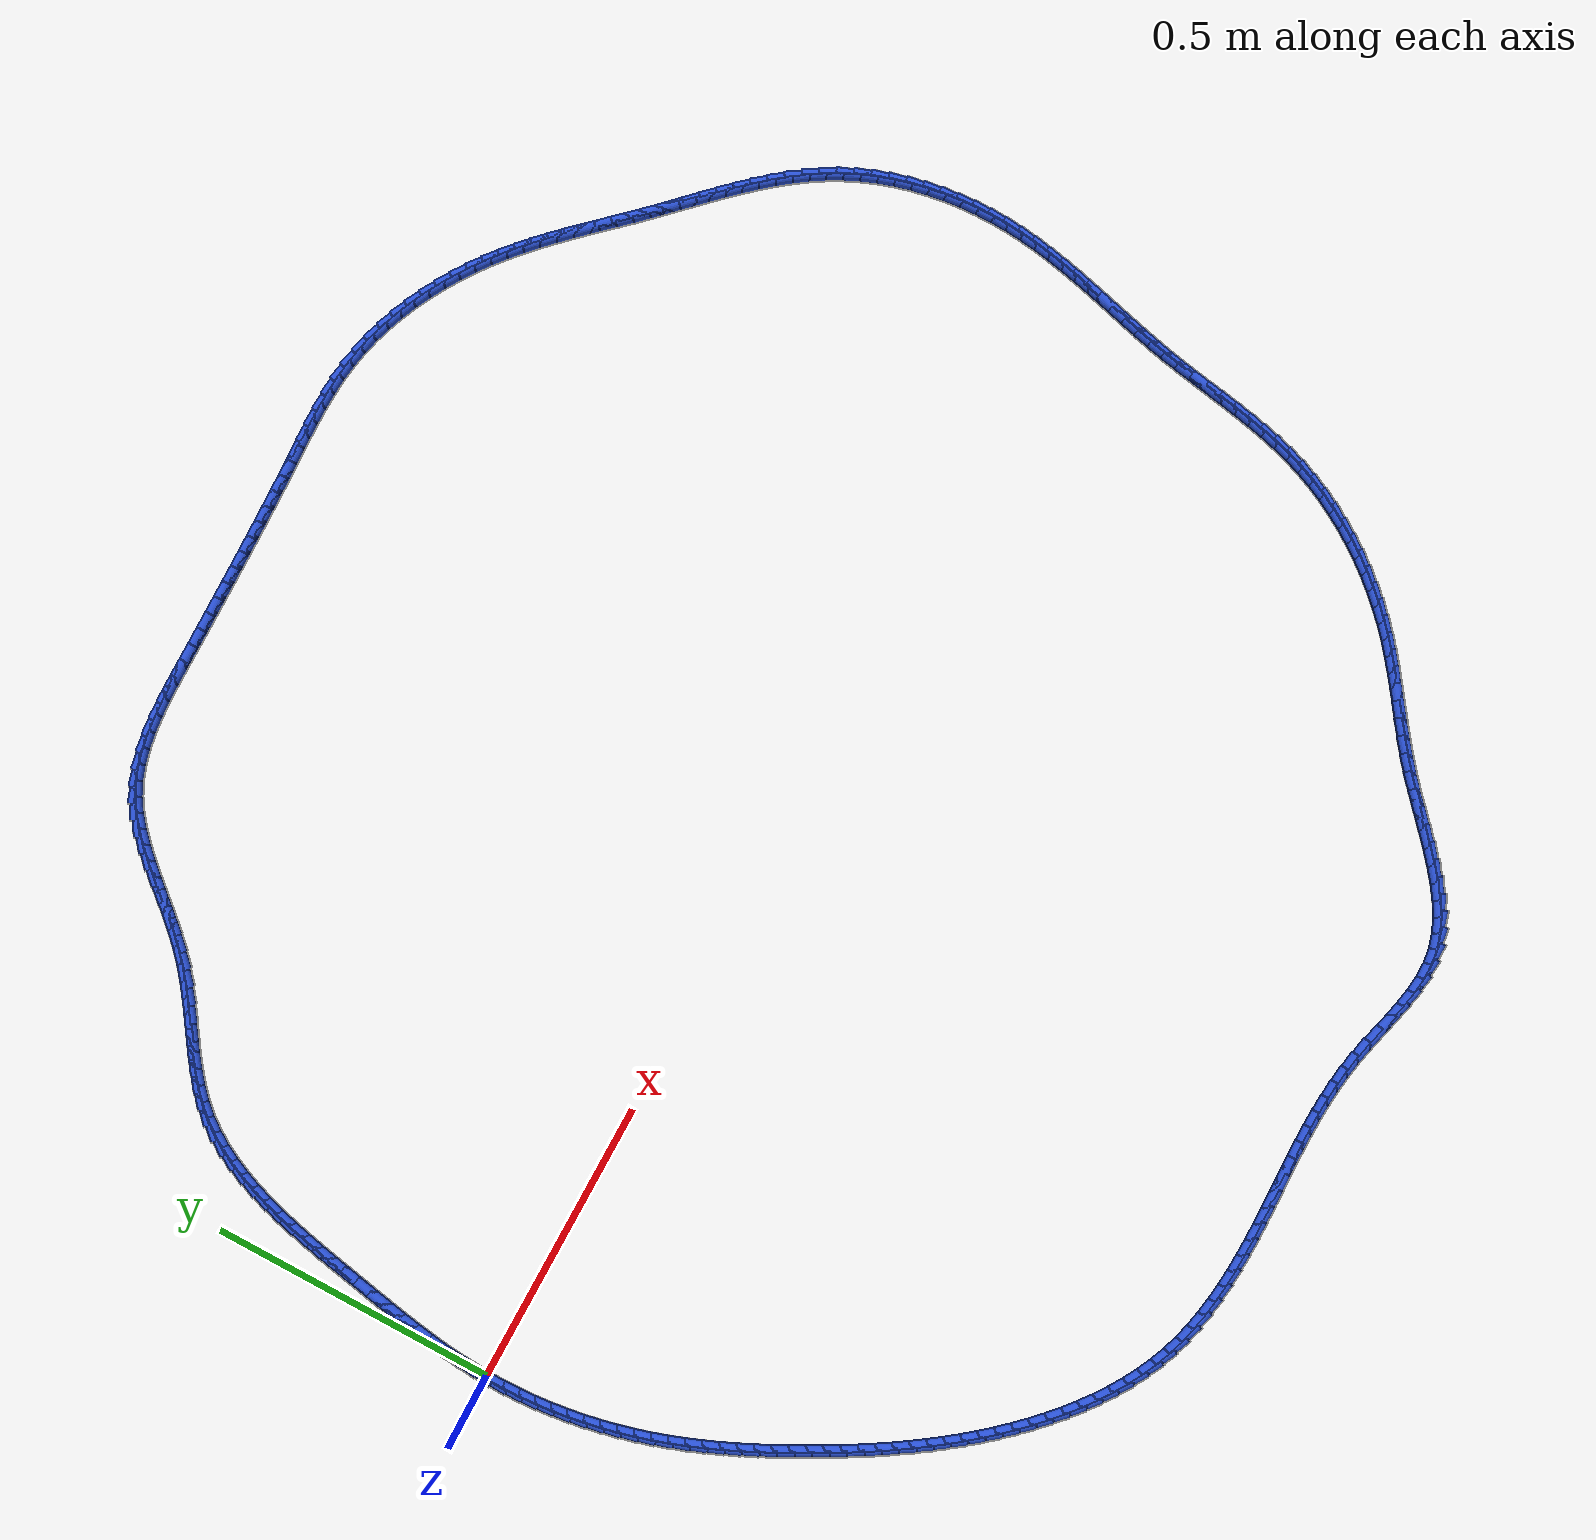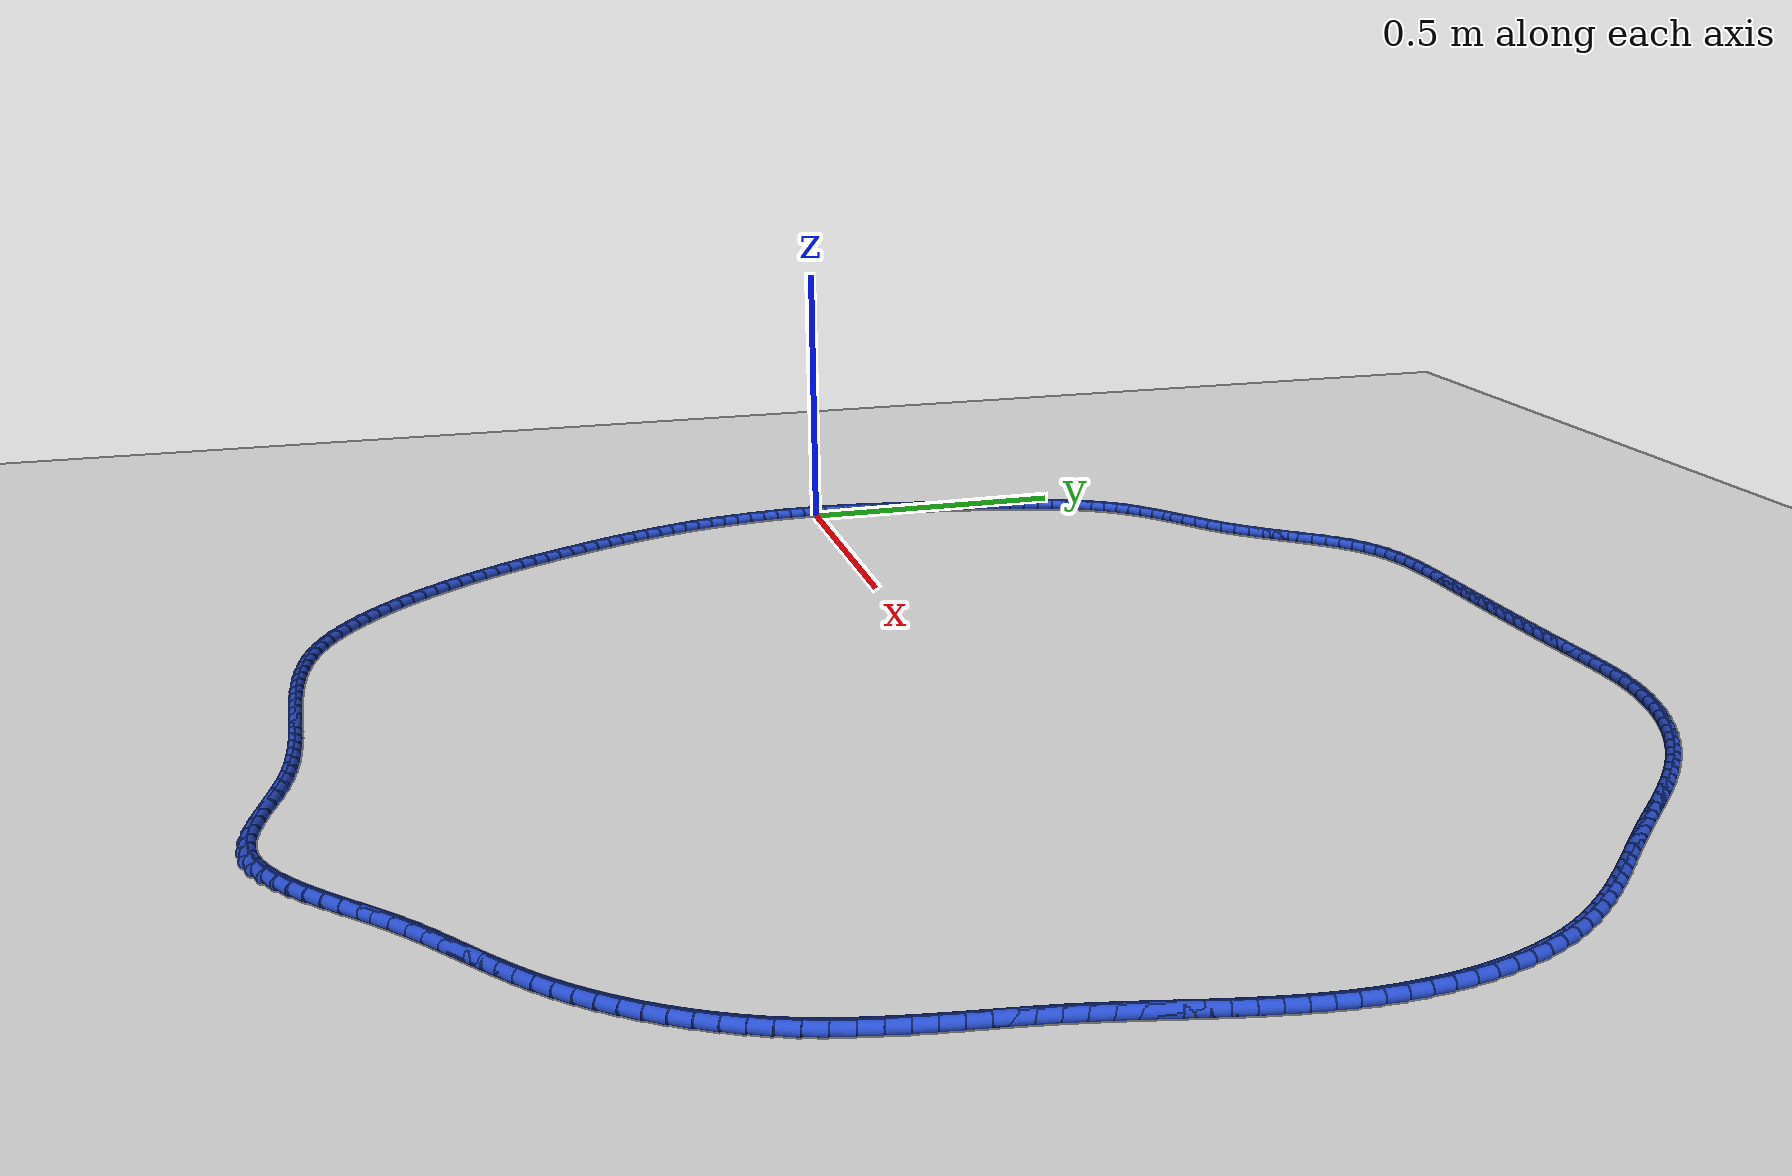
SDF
<sdf version="1.6">
 <world name="default">
  <light name="sun" type="directional">
   <pose>0 0 10 0 -0 0</pose>
   <diffuse>0.8 0.8 0.8 1</diffuse>
   <specular>0.2 0.2 0.2 1</specular>
   <attenuation>
    <range>1000</range>
    <constant>0.9</constant>
    <linear>0.01</linear>
    <quadratic>0.001</quadratic>
   </attenuation>
   <direction>-0.5 0.1 -0.9</direction>
  </light>
  <model name="ground_plane">
   <static>1</static>
   <link name="link">
    <collision name="collision">
     <geometry><plane><normal>0 0 1</normal><size>100 100</size></plane></geometry>
     <surface><friction><ode><mu>100</mu><mu2>50</mu2></ode></friction></surface>
    </collision>
    <visual name="visual">
     <cast_shadows>0</cast_shadows>
     <geometry><plane><normal>0 0 1</normal><size>100 100</size></plane></geometry>
     <material>
      <script><uri>file://media/materials/scripts/gazebo.material</uri><name>Gazebo/WhiteGlow</name></script>
     </material>
    </visual>
   </link>
  </model>
  <gravity>0 0 -9.8</gravity>
  <magnetic_field>6e-06 2.3e-05 -4.2e-05</magnetic_field>
  <atmosphere type="adiabatic"/>
  <physics name="default_physics" default="0" type="ode">
   <max_step_size>0.001</max_step_size>
   <real_time_factor>1</real_time_factor>
   <real_time_update_rate>1000</real_time_update_rate>
  </physics>
  <scene><ambient>0.4 0.4 0.4 1</ambient><background>0.7 0.7 0.7 1</background><shadows>1</shadows></scene>
  <spherical_coordinates>
   <surface_model>EARTH_WGS84</surface_model>
   <latitude_deg>0</latitude_deg>
   <longitude_deg>0</longitude_deg>
   <elevation>0</elevation>
   <heading_deg>0</heading_deg>
  </spherical_coordinates>
  <model name="line">
   <link name="link_0">
    <pose>3.469446951953614e-18 1.3877787807814457e-17 0.01 0 1.57 1.5299129188031793</pose>
    <collision name="collision">
     <geometry><cylinder><radius>0.01</radius><length>0.08</length></cylinder></geometry>
    </collision>
    <visual name="visual">
     <material>
      <script><name>Gazebo/Blue</name><uri>file://media/materials/scripts/gazebo.material</uri></script>
     </material>
     <geometry><cylinder><radius>0.01</radius><length>0.08</length></cylinder></geometry>
    </visual>
   </link>
   <link name="link_1">
    <pose>0.0011530025170490552 0.02818649680976999 0.01 0 1.57 1.497769813567669</pose>
    <collision name="collision">
     <geometry><cylinder><radius>0.01</radius><length>0.08</length></cylinder></geometry>
    </collision>
    <visual name="visual">
     <material>
      <script><name>Gazebo/Blue</name><uri>file://media/materials/scripts/gazebo.material</uri></script>
     </material>
     <geometry><cylinder><radius>0.01</radius><length>0.08</length></cylinder></geometry>
    </visual>
   </link>
   <link name="link_2">
    <pose>0.0032068903203694775 0.056261717356643946 0.01 0 1.57 1.4693903626771059</pose>
    <collision name="collision">
     <geometry><cylinder><radius>0.01</radius><length>0.08</length></cylinder></geometry>
    </collision>
    <visual name="visual">
     <material>
      <script><name>Gazebo/Blue</name><uri>file://media/materials/scripts/gazebo.material</uri></script>
     </material>
     <geometry><cylinder><radius>0.01</radius><length>0.08</length></cylinder></geometry>
    </visual>
   </link>
   <link name="link_3">
    <pose>0.006057501423697899 0.08427617703042298 0.01 0 1.57 1.4449422129983254</pose>
    <collision name="collision">
     <geometry><cylinder><radius>0.01</radius><length>0.08</length></cylinder></geometry>
    </collision>
    <visual name="visual">
     <material>
      <script><name>Gazebo/Blue</name><uri>file://media/materials/scripts/gazebo.material</uri></script>
     </material>
     <geometry><cylinder><radius>0.01</radius><length>0.08</length></cylinder></geometry>
    </visual>
   </link>
   <link name="link_4">
    <pose>0.009600673840770941 0.11228039122090795 0.01 0 1.57 1.4245263946095714</pose>
    <collision name="collision">
     <geometry><cylinder><radius>0.01</radius><length>0.08</length></cylinder></geometry>
    </collision>
    <visual name="visual">
     <material>
      <script><name>Gazebo/Blue</name><uri>file://media/materials/scripts/gazebo.material</uri></script>
     </material>
     <geometry><cylinder><radius>0.01</radius><length>0.08</length></cylinder></geometry>
    </visual>
   </link>
   <link name="link_5">
    <pose>0.013732245585325232 0.14032487531789986 0.01 0 1.57 1.4081871204633614</pose>
    <collision name="collision">
     <geometry><cylinder><radius>0.01</radius><length>0.08</length></cylinder></geometry>
    </collision>
    <visual name="visual">
     <material>
      <script><name>Gazebo/Blue</name><uri>file://media/materials/scripts/gazebo.material</uri></script>
     </material>
     <geometry><cylinder><radius>0.01</radius><length>0.08</length></cylinder></geometry>
    </visual>
   </link>
   <link name="link_6">
    <pose>0.018348054671097402 0.1684601447111998 0.01 0 1.57 1.3959217323673576</pose>
    <collision name="collision">
     <geometry><cylinder><radius>0.01</radius><length>0.08</length></cylinder></geometry>
    </collision>
    <visual name="visual">
     <material>
      <script><name>Gazebo/Blue</name><uri>file://media/materials/scripts/gazebo.material</uri></script>
     </material>
     <geometry><cylinder><radius>0.01</radius><length>0.08</length></cylinder></geometry>
    </visual>
   </link>
   <link name="link_7">
    <pose>0.023343939111824065 0.19673671479060856 0.01 0 1.57 1.3876897735565916</pose>
    <collision name="collision">
     <geometry><cylinder><radius>0.01</radius><length>0.08</length></cylinder></geometry>
    </collision>
    <visual name="visual">
     <material>
      <script><name>Gazebo/Blue</name><uri>file://media/materials/scripts/gazebo.material</uri></script>
     </material>
     <geometry><cylinder><radius>0.01</radius><length>0.08</length></cylinder></geometry>
    </visual>
   </link>
   <link name="link_8">
    <pose>0.028615736921241853 0.22520510094592724 0.01 0 1.57 1.3834205681677068</pose>
    <collision name="collision">
     <geometry><cylinder><radius>0.01</radius><length>0.08</length></cylinder></geometry>
    </collision>
    <visual name="visual">
     <material>
      <script><name>Gazebo/Blue</name><uri>file://media/materials/scripts/gazebo.material</uri></script>
     </material>
     <geometry><cylinder><radius>0.01</radius><length>0.08</length></cylinder></geometry>
    </visual>
   </link>
   <link name="link_9">
    <pose>0.034059286113087395 0.25391581856695683 0.01 0 1.57 1.382868552914791</pose>
    <collision name="collision">
     <geometry><cylinder><radius>0.01</radius><length>0.08</length></cylinder></geometry>
    </collision>
    <visual name="visual">
     <material>
      <script><name>Gazebo/Blue</name><uri>file://media/materials/scripts/gazebo.material</uri></script>
     </material>
     <geometry><cylinder><radius>0.01</radius><length>0.08</length></cylinder></geometry>
    </visual>
   </link>
   <link name="link_10">
    <pose>0.03957434939670133 0.2829162420170616 0.01 0 1.57 1.3815614575415698</pose>
    <collision name="collision">
     <geometry><cylinder><radius>0.01</radius><length>0.08</length></cylinder></geometry>
    </collision>
    <visual name="visual">
     <material>
      <script><name>Gazebo/Blue</name><uri>file://media/materials/scripts/gazebo.material</uri></script>
     </material>
     <geometry><cylinder><radius>0.01</radius><length>0.08</length></cylinder></geometry>
    </visual>
   </link>
   <link name="link_11">
    <pose>0.045175639563653745 0.3121617483982633 0.01 0 1.57 1.37456282095957</pose>
    <collision name="collision">
     <geometry><cylinder><radius>0.01</radius><length>0.08</length></cylinder></geometry>
    </collision>
    <visual name="visual">
     <material>
      <script><name>Gazebo/Blue</name><uri>file://media/materials/scripts/gazebo.material</uri></script>
     </material>
     <geometry><cylinder><radius>0.01</radius><length>0.08</length></cylinder></geometry>
    </visual>
   </link>
   <link name="link_12">
    <pose>0.051008475458380484 0.3415031877087713 0.01 0 1.57 1.3615995437440158</pose>
    <collision name="collision">
     <geometry><cylinder><radius>0.01</radius><length>0.08</length></cylinder></geometry>
    </collision>
    <visual name="visual">
     <material>
      <script><name>Gazebo/Blue</name><uri>file://media/materials/scripts/gazebo.material</uri></script>
     </material>
     <geometry><cylinder><radius>0.01</radius><length>0.08</length></cylinder></geometry>
    </visual>
   </link>
   <link name="link_13">
    <pose>0.05722524782726675 0.3707857501369087 0.01 0 1.57 1.3425315483709672</pose>
    <collision name="collision">
     <geometry><cylinder><radius>0.01</radius><length>0.08</length></cylinder></geometry>
    </collision>
    <visual name="visual">
     <material>
      <script><name>Gazebo/Blue</name><uri>file://media/materials/scripts/gazebo.material</uri></script>
     </material>
     <geometry><cylinder><radius>0.01</radius><length>0.08</length></cylinder></geometry>
    </visual>
   </link>
   <link name="link_14">
    <pose>0.06397834741669772 0.39985462587099874 0.01 0 1.57 1.3170902846725199</pose>
    <collision name="collision">
     <geometry><cylinder><radius>0.01</radius><length>0.08</length></cylinder></geometry>
    </collision>
    <visual name="visual">
     <material>
      <script><name>Gazebo/Blue</name><uri>file://media/materials/scripts/gazebo.material</uri></script>
     </material>
     <geometry><cylinder><radius>0.01</radius><length>0.08</length></cylinder></geometry>
    </visual>
   </link>
   <link name="link_15">
    <pose>0.07142016497305857 0.42855500509936445 0.01 0 1.57 1.2848901855311876</pose>
    <collision name="collision">
     <geometry><cylinder><radius>0.01</radius><length>0.08</length></cylinder></geometry>
    </collision>
    <visual name="visual">
     <material>
      <script><name>Gazebo/Blue</name><uri>file://media/materials/scripts/gazebo.material</uri></script>
     </material>
     <geometry><cylinder><radius>0.01</radius><length>0.08</length></cylinder></geometry>
    </visual>
   </link>
   <link name="link_16">
    <pose>0.07970309124273453 0.4567320780103295 0.01 0 1.57 1.2454464794236753</pose>
    <collision name="collision">
     <geometry><cylinder><radius>0.01</radius><length>0.08</length></cylinder></geometry>
    </collision>
    <visual name="visual">
     <material>
      <script><name>Gazebo/Blue</name><uri>file://media/materials/scripts/gazebo.material</uri></script>
     </material>
     <geometry><cylinder><radius>0.01</radius><length>0.08</length></cylinder></geometry>
    </visual>
   </link>
   <link name="link_17">
    <pose>0.0889795169721107 0.48423103479221624 0.01 0 1.57 1.1982060074406884</pose>
    <collision name="collision">
     <geometry><cylinder><radius>0.01</radius><length>0.08</length></cylinder></geometry>
    </collision>
    <visual name="visual">
     <material>
      <script><name>Gazebo/Blue</name><uri>file://media/materials/scripts/gazebo.material</uri></script>
     </material>
     <geometry><cylinder><radius>0.01</radius><length>0.08</length></cylinder></geometry>
    </visual>
   </link>
   <link name="link_18">
    <pose>0.09940183290757239 0.5108970656333486 0.01 0 1.57 1.1425999506336486</pose>
    <collision name="collision">
     <geometry><cylinder><radius>0.01</radius><length>0.08</length></cylinder></geometry>
    </collision>
    <visual name="visual">
     <material>
      <script><name>Gazebo/Blue</name><uri>file://media/materials/scripts/gazebo.material</uri></script>
     </material>
     <geometry><cylinder><radius>0.01</radius><length>0.08</length></cylinder></geometry>
    </visual>
   </link>
   <link name="link_19">
    <pose>0.11112242979550464 0.536575360722049 0.01 0 1.57 1.0781287932297328</pose>
    <collision name="collision">
     <geometry><cylinder><radius>0.01</radius><length>0.08</length></cylinder></geometry>
    </collision>
    <visual name="visual">
     <material>
      <script><name>Gazebo/Blue</name><uri>file://media/materials/scripts/gazebo.material</uri></script>
     </material>
     <geometry><cylinder><radius>0.01</radius><length>0.08</length></cylinder></geometry>
    </visual>
   </link>
   <link name="link_20">
    <pose>0.12429369838229275 0.5611111102466413 0.01 0 1.57 1.00448799987924</pose>
    <collision name="collision">
     <geometry><cylinder><radius>0.01</radius><length>0.08</length></cylinder></geometry>
    </collision>
    <visual name="visual">
     <material>
      <script><name>Gazebo/Blue</name><uri>file://media/materials/scripts/gazebo.material</uri></script>
     </material>
     <geometry><cylinder><radius>0.01</radius><length>0.08</length></cylinder></geometry>
    </visual>
   </link>
   <link name="link_21">
    <pose>0.1390680294143219 0.5843495043954485 0.01 0 1.57 0.9217337579621993</pose>
    <collision name="collision">
     <geometry><cylinder><radius>0.01</radius><length>0.08</length></cylinder></geometry>
    </collision>
    <visual name="visual">
     <material>
      <script><name>Gazebo/Blue</name><uri>file://media/materials/scripts/gazebo.material</uri></script>
     </material>
     <geometry><cylinder><radius>0.01</radius><length>0.08</length></cylinder></geometry>
    </visual>
   </link>
   <link name="link_22">
    <pose>0.1555978136379772 0.6061357333567934 0.01 0 1.57 0.8310435819316709</pose>
    <collision name="collision">
     <geometry><cylinder><radius>0.01</radius><length>0.08</length></cylinder></geometry>
    </collision>
    <visual name="visual">
     <material>
      <script><name>Gazebo/Blue</name><uri>file://media/materials/scripts/gazebo.material</uri></script>
     </material>
     <geometry><cylinder><radius>0.01</radius><length>0.08</length></cylinder></geometry>
    </visual>
   </link>
   <link name="link_23">
    <pose>0.17402436940957766 0.6263262047059167 0.01 0 1.57 0.7464101622358386</pose>
    <collision name="collision">
     <geometry><cylinder><radius>0.01</radius><length>0.08</length></cylinder></geometry>
    </collision>
    <visual name="visual">
     <material>
      <script><name>Gazebo/Blue</name><uri>file://media/materials/scripts/gazebo.material</uri></script>
     </material>
     <geometry><cylinder><radius>0.01</radius><length>0.08</length></cylinder></geometry>
    </visual>
   </link>
   <link name="link_24">
    <pose>0.1942429356074061 0.6450266279935991 0.01 0 1.57 0.6811563899036511</pose>
    <collision name="collision">
     <geometry><cylinder><radius>0.01</radius><length>0.08</length></cylinder></geometry>
    </collision>
    <visual name="visual">
     <material>
      <script><name>Gazebo/Blue</name><uri>file://media/materials/scripts/gazebo.material</uri></script>
     </material>
     <geometry><cylinder><radius>0.01</radius><length>0.08</length></cylinder></geometry>
    </visual>
   </link>
   <link name="link_25">
    <pose>0.21590734890573032 0.662587276221589 0.01 0 1.57 0.6354635268026902</pose>
    <collision name="collision">
     <geometry><cylinder><radius>0.01</radius><length>0.08</length></cylinder></geometry>
    </collision>
    <visual name="visual">
     <material>
      <script><name>Gazebo/Blue</name><uri>file://media/materials/scripts/gazebo.material</uri></script>
     </material>
     <geometry><cylinder><radius>0.01</radius><length>0.08</length></cylinder></geometry>
    </visual>
   </link>
   <link name="link_26">
    <pose>0.2386613091515491 0.679368691964231 0.01 0 1.57 0.6084845085814978</pose>
    <collision name="collision">
     <geometry><cylinder><radius>0.01</radius><length>0.08</length></cylinder></geometry>
    </collision>
    <visual name="visual">
     <material>
      <script><name>Gazebo/Blue</name><uri>file://media/materials/scripts/gazebo.material</uri></script>
     </material>
     <geometry><cylinder><radius>0.01</radius><length>0.08</length></cylinder></geometry>
    </visual>
   </link>
   <link name="link_27">
    <pose>0.262148516191861 0.6957314177958686 0.01 0 1.57 0.5993784056537174</pose>
    <collision name="collision">
     <geometry><cylinder><radius>0.01</radius><length>0.08</length></cylinder></geometry>
    </collision>
    <visual name="visual">
     <material>
      <script><name>Gazebo/Blue</name><uri>file://media/materials/scripts/gazebo.material</uri></script>
     </material>
     <geometry><cylinder><radius>0.01</radius><length>0.08</length></cylinder></geometry>
    </visual>
   </link>
   <link name="link_28">
    <pose>0.28601266987366486 0.712035996290846 0.01 0 1.57 0.6075610244165411</pose>
    <collision name="collision">
     <geometry><cylinder><radius>0.01</radius><length>0.08</length></cylinder></geometry>
    </collision>
    <visual name="visual">
     <material>
      <script><name>Gazebo/Blue</name><uri>file://media/materials/scripts/gazebo.material</uri></script>
     </material>
     <geometry><cylinder><radius>0.01</radius><length>0.08</length></cylinder></geometry>
    </visual>
   </link>
   <link name="link_29">
    <pose>0.3098974700439591 0.7286429700235072 0.01 0 1.57 0.6327636757870426</pose>
    <collision name="collision">
     <geometry><cylinder><radius>0.01</radius><length>0.08</length></cylinder></geometry>
    </collision>
    <visual name="visual">
     <material>
      <script><name>Gazebo/Blue</name><uri>file://media/materials/scripts/gazebo.material</uri></script>
     </material>
     <geometry><cylinder><radius>0.01</radius><length>0.08</length></cylinder></geometry>
    </visual>
   </link>
   <link name="link_30">
    <pose>0.3334466165497426 0.745912881568196 0.01 0 1.57 0.674944660335149</pose>
    <collision name="collision">
     <geometry><cylinder><radius>0.01</radius><length>0.08</length></cylinder></geometry>
    </collision>
    <visual name="visual">
     <material>
      <script><name>Gazebo/Blue</name><uri>file://media/materials/scripts/gazebo.material</uri></script>
     </material>
     <geometry><cylinder><radius>0.01</radius><length>0.08</length></cylinder></geometry>
    </visual>
   </link>
   <link name="link_31">
    <pose>0.35630380923801414 0.7642062734992568 0.01 0 1.57 0.7331527381415547</pose>
    <collision name="collision">
     <geometry><cylinder><radius>0.01</radius><length>0.08</length></cylinder></geometry>
    </collision>
    <visual name="visual">
     <material>
      <script><name>Gazebo/Blue</name><uri>file://media/materials/scripts/gazebo.material</uri></script>
     </material>
     <geometry><cylinder><radius>0.01</radius><length>0.08</length></cylinder></geometry>
    </visual>
   </link>
   <link name="link_32">
    <pose>0.3781293280893622 0.7838625825707028 0.01 0 1.57 0.7894097712730372</pose>
    <collision name="collision">
     <geometry><cylinder><radius>0.01</radius><length>0.08</length></cylinder></geometry>
    </collision>
    <visual name="visual">
     <material>
      <script><name>Gazebo/Blue</name><uri>file://media/materials/scripts/gazebo.material</uri></script>
     </material>
     <geometry><cylinder><radius>0.01</radius><length>0.08</length></cylinder></geometry>
    </visual>
   </link>
   <link name="link_33">
    <pose>0.39890776860618427 0.8048084053687371 0.01 0 1.57 0.8278243296899235</pose>
    <collision name="collision">
     <geometry><cylinder><radius>0.01</radius><length>0.08</length></cylinder></geometry>
    </collision>
    <visual name="visual">
     <material>
      <script><name>Gazebo/Blue</name><uri>file://media/materials/scripts/gazebo.material</uri></script>
     </material>
     <geometry><cylinder><radius>0.01</radius><length>0.08</length></cylinder></geometry>
    </visual>
   </link>
   <link name="link_34">
    <pose>0.4189192064748526 0.8265942044972698 0.01 0 1.57 0.8483203543843909</pose>
    <collision name="collision">
     <geometry><cylinder><radius>0.01</radius><length>0.08</length></cylinder></geometry>
    </collision>
    <visual name="visual">
     <material>
      <script><name>Gazebo/Blue</name><uri>file://media/materials/scripts/gazebo.material</uri></script>
     </material>
     <geometry><cylinder><radius>0.01</radius><length>0.08</length></cylinder></geometry>
    </visual>
   </link>
   <link name="link_35">
    <pose>0.43845451476832803 0.8487566979362532 0.01 0 1.57 0.8511040692108328</pose>
    <collision name="collision">
     <geometry><cylinder><radius>0.01</radius><length>0.08</length></cylinder></geometry>
    </collision>
    <visual name="visual">
     <material>
      <script><name>Gazebo/Blue</name><uri>file://media/materials/scripts/gazebo.material</uri></script>
     </material>
     <geometry><cylinder><radius>0.01</radius><length>0.08</length></cylinder></geometry>
    </visual>
   </link>
   <link name="link_36">
    <pose>0.45780456655957136 0.8708326036656392 0.01 0 1.57 0.8358745657494786</pose>
    <collision name="collision">
     <geometry><cylinder><radius>0.01</radius><length>0.08</length></cylinder></geometry>
    </collision>
    <visual name="visual">
     <material>
      <script><name>Gazebo/Blue</name><uri>file://media/materials/scripts/gazebo.material</uri></script>
     </material>
     <geometry><cylinder><radius>0.01</radius><length>0.08</length></cylinder></geometry>
    </visual>
   </link>
   <link name="link_37">
    <pose>0.47726023492154324 0.8923586396653801 0.01 0 1.57 0.801765475457663</pose>
    <collision name="collision">
     <geometry><cylinder><radius>0.01</radius><length>0.08</length></cylinder></geometry>
    </collision>
    <visual name="visual">
     <material>
      <script><name>Gazebo/Blue</name><uri>file://media/materials/scripts/gazebo.material</uri></script>
     </material>
     <geometry><cylinder><radius>0.01</radius><length>0.08</length></cylinder></geometry>
    </visual>
   </link>
   <link name="link_38">
    <pose>0.49711239292720466 0.912871523915428 0.01 0 1.57 0.7474370438369248</pose>
    <collision name="collision">
     <geometry><cylinder><radius>0.01</radius><length>0.08</length></cylinder></geometry>
    </collision>
    <visual name="visual">
     <material>
      <script><name>Gazebo/Blue</name><uri>file://media/materials/scripts/gazebo.material</uri></script>
     </material>
     <geometry><cylinder><radius>0.01</radius><length>0.08</length></cylinder></geometry>
    </visual>
   </link>
   <link name="link_39">
    <pose>0.5176519136495165 0.9319079743957353 0.01 0 1.57 0.6714032635390633</pose>
    <collision name="collision">
     <geometry><cylinder><radius>0.01</radius><length>0.08</length></cylinder></geometry>
    </collision>
    <visual name="visual">
     <material>
      <script><name>Gazebo/Blue</name><uri>file://media/materials/scripts/gazebo.material</uri></script>
     </material>
     <geometry><cylinder><radius>0.01</radius><length>0.08</length></cylinder></geometry>
    </visual>
   </link>
   <link name="link_40">
    <pose>0.5391696701614394 0.9490047090862536 0.01 0 1.57 0.5727347406190535</pose>
    <collision name="collision">
     <geometry><cylinder><radius>0.01</radius><length>0.08</length></cylinder></geometry>
    </collision>
    <visual name="visual">
     <material>
      <script><name>Gazebo/Blue</name><uri>file://media/materials/scripts/gazebo.material</uri></script>
     </material>
     <geometry><cylinder><radius>0.01</radius><length>0.08</length></cylinder></geometry>
    </visual>
   </link>
   <link name="link_41">
    <pose>0.561956535535934 0.9636984459669355 0.01 0 1.57 0.45365566244552513</pose>
    <collision name="collision">
     <geometry><cylinder><radius>0.01</radius><length>0.08</length></cylinder></geometry>
    </collision>
    <visual name="visual">
     <material>
      <script><name>Gazebo/Blue</name><uri>file://media/materials/scripts/gazebo.material</uri></script>
     </material>
     <geometry><cylinder><radius>0.01</radius><length>0.08</length></cylinder></geometry>
    </visual>
   </link>
   <link name="link_42">
    <pose>0.5862822608783981 0.9755589823066295 0.01 0 1.57 0.3371239684838181</pose>
    <collision name="collision">
     <geometry><cylinder><radius>0.01</radius><length>0.08</length></cylinder></geometry>
    </collision>
    <visual name="visual">
     <material>
      <script><name>Gazebo/Blue</name><uri>file://media/materials/scripts/gazebo.material</uri></script>
     </material>
     <geometry><cylinder><radius>0.01</radius><length>0.08</length></cylinder></geometry>
    </visual>
   </link>
   <link name="link_43">
    <pose>0.6121228170552429 0.9846162070473866 0.01 0 1.57 0.23948480689791402</pose>
    <collision name="collision">
     <geometry><cylinder><radius>0.01</radius><length>0.08</length></cylinder></geometry>
    </collision>
    <visual name="visual">
     <material>
      <script><name>Gazebo/Blue</name><uri>file://media/materials/scripts/gazebo.material</uri></script>
     </material>
     <geometry><cylinder><radius>0.01</radius><length>0.08</length></cylinder></geometry>
    </visual>
   </link>
   <link name="link_44">
    <pose>0.6392388957476413 0.9912371596519429 0.01 0 1.57 0.16059064361516703</pose>
    <collision name="collision">
     <geometry><cylinder><radius>0.01</radius><length>0.08</length></cylinder></geometry>
    </collision>
    <visual name="visual">
     <material>
      <script><name>Gazebo/Blue</name><uri>file://media/materials/scripts/gazebo.material</uri></script>
     </material>
     <geometry><cylinder><radius>0.01</radius><length>0.08</length></cylinder></geometry>
    </visual>
   </link>
   <link name="link_45">
    <pose>0.6673862441356496 0.9957966232073175 0.01 0 1.57 0.09896099443434532</pose>
    <collision name="collision">
     <geometry><cylinder><radius>0.01</radius><length>0.08</length></cylinder></geometry>
    </collision>
    <visual name="visual">
     <material>
      <script><name>Gazebo/Blue</name><uri>file://media/materials/scripts/gazebo.material</uri></script>
     </material>
     <geometry><cylinder><radius>0.01</radius><length>0.08</length></cylinder></geometry>
    </visual>
   </link>
   <link name="link_46">
    <pose>0.6963206093993242 0.9986693808005298 0.01 0 1.57 0.05290129870291687</pose>
    <collision name="collision">
     <geometry><cylinder><radius>0.01</radius><length>0.08</length></cylinder></geometry>
    </collision>
    <visual name="visual">
     <material>
      <script><name>Gazebo/Blue</name><uri>file://media/materials/scripts/gazebo.material</uri></script>
     </material>
     <geometry><cylinder><radius>0.01</radius><length>0.08</length></cylinder></geometry>
    </visual>
   </link>
   <link name="link_47">
    <pose>0.7257977387187203 1.0002302155185985 0.01 0 1.57 0.02094341971740238</pose>
    <collision name="collision">
     <geometry><cylinder><radius>0.01</radius><length>0.08</length></cylinder></geometry>
    </collision>
    <visual name="visual">
     <material>
      <script><name>Gazebo/Blue</name><uri>file://media/materials/scripts/gazebo.material</uri></script>
     </material>
     <geometry><cylinder><radius>0.01</radius><length>0.08</length></cylinder></geometry>
    </visual>
   </link>
   <link name="link_48">
    <pose>0.7555733792738945 1.0008539104485432 0.01 0 1.57 0.0020562638327657145</pose>
    <collision name="collision">
     <geometry><cylinder><radius>0.01</radius><length>0.08</length></cylinder></geometry>
    </collision>
    <visual name="visual">
     <material>
      <script><name>Gazebo/Blue</name><uri>file://media/materials/scripts/gazebo.material</uri></script>
     </material>
     <geometry><cylinder><radius>0.01</radius><length>0.08</length></cylinder></geometry>
    </visual>
   </link>
   <link name="link_49">
    <pose>0.7854032782449024 1.000915248677383 0.01 0 1.57 -0.004418155447898515</pose>
    <collision name="collision">
     <geometry><cylinder><radius>0.01</radius><length>0.08</length></cylinder></geometry>
    </collision>
    <visual name="visual">
     <material>
      <script><name>Gazebo/Blue</name><uri>file://media/materials/scripts/gazebo.material</uri></script>
     </material>
     <geometry><cylinder><radius>0.01</radius><length>0.08</length></cylinder></geometry>
    </visual>
   </link>
   <link name="link_50">
    <pose>0.8150468088220629 1.0007842780990812 0.01 0 1.57 -0.003809452947665123</pose>
    <collision name="collision">
     <geometry><cylinder><radius>0.01</radius><length>0.08</length></cylinder></geometry>
    </collision>
    <visual name="visual">
     <material>
      <script><name>Gazebo/Blue</name><uri>file://media/materials/scripts/gazebo.material</uri></script>
     </material>
     <geometry><cylinder><radius>0.01</radius><length>0.08</length></cylinder></geometry>
    </visual>
   </link>
   <link name="link_51">
    <pose>0.8443847401512636 1.0006725160894727 0.01 0 1.57 -0.002522411451427157</pose>
    <collision name="collision">
     <geometry><cylinder><radius>0.01</radius><length>0.08</length></cylinder></geometry>
    </collision>
    <visual name="visual">
     <material>
      <script><name>Gazebo/Blue</name><uri>file://media/materials/scripts/gazebo.material</uri></script>
     </material>
     <geometry><cylinder><radius>0.01</radius><length>0.08</length></cylinder></geometry>
    </visual>
   </link>
   <link name="link_52">
    <pose>0.8734450706908279 1.000599213823474 0.01 0 1.57 -0.0009421544616380929</pose>
    <collision name="collision">
     <geometry><cylinder><radius>0.01</radius><length>0.08</length></cylinder></geometry>
    </collision>
    <visual name="visual">
     <material>
      <script><name>Gazebo/Blue</name><uri>file://media/materials/scripts/gazebo.material</uri></script>
     </material>
     <geometry><cylinder><radius>0.01</radius><length>0.08</length></cylinder></geometry>
    </visual>
   </link>
   <link name="link_53">
    <pose>0.9022646519438626 1.00057206131838 0.01 0 1.57 0.0009326097486870044</pose>
    <collision name="collision">
     <geometry><cylinder><radius>0.01</radius><length>0.08</length></cylinder></geometry>
    </collision>
    <visual name="visual">
     <material>
      <script><name>Gazebo/Blue</name><uri>file://media/materials/scripts/gazebo.material</uri></script>
     </material>
     <geometry><cylinder><radius>0.01</radius><length>0.08</length></cylinder></geometry>
    </visual>
   </link>
   <link name="link_54">
    <pose>0.9308803354134749 1.0005987485914862 0.01 0 1.57 0.0031009142990244425</pose>
    <collision name="collision">
     <geometry><cylinder><radius>0.01</radius><length>0.08</length></cylinder></geometry>
    </collision>
    <visual name="visual">
     <material>
      <script><name>Gazebo/Blue</name><uri>file://media/materials/scripts/gazebo.material</uri></script>
     </material>
     <geometry><cylinder><radius>0.01</radius><length>0.08</length></cylinder></geometry>
    </visual>
   </link>
   <link name="link_55">
    <pose>0.9593289726027725 1.0006869656600899 0.01 0 1.57 0.005559460407578012</pose>
    <collision name="collision">
     <geometry><cylinder><radius>0.01</radius><length>0.08</length></cylinder></geometry>
    </collision>
    <visual name="visual">
     <material>
      <script><name>Gazebo/Blue</name><uri>file://media/materials/scripts/gazebo.material</uri></script>
     </material>
     <geometry><cylinder><radius>0.01</radius><length>0.08</length></cylinder></geometry>
    </visual>
   </link>
   <link name="link_56">
    <pose>0.9876474150148628 1.0008444025414862 0.01 0 1.57 0.008302586487947673</pose>
    <collision name="collision">
     <geometry><cylinder><radius>0.01</radius><length>0.08</length></cylinder></geometry>
    </collision>
    <visual name="visual">
     <material>
      <script><name>Gazebo/Blue</name><uri>file://media/materials/scripts/gazebo.material</uri></script>
     </material>
     <geometry><cylinder><radius>0.01</radius><length>0.08</length></cylinder></geometry>
    </visual>
   </link>
   <link name="link_57">
    <pose>1.0158725141528524 1.0010787492529711 0.01 0 1.57 0.011322282481975855</pose>
    <collision name="collision">
     <geometry><cylinder><radius>0.01</radius><length>0.08</length></cylinder></geometry>
    </collision>
    <visual name="visual">
     <material>
      <script><name>Gazebo/Blue</name><uri>file://media/materials/scripts/gazebo.material</uri></script>
     </material>
     <geometry><cylinder><radius>0.01</radius><length>0.08</length></cylinder></geometry>
    </visual>
   </link>
   <link name="link_58">
    <pose>1.0440411215198488 1.001397695811841 0.01 0 1.57 0.014608250772847173</pose>
    <collision name="collision">
     <geometry><cylinder><radius>0.01</radius><length>0.08</length></cylinder></geometry>
    </collision>
    <visual name="visual">
     <material>
      <script><name>Gazebo/Blue</name><uri>file://media/materials/scripts/gazebo.material</uri></script>
     </material>
     <geometry><cylinder><radius>0.01</radius><length>0.08</length></cylinder></geometry>
    </visual>
   </link>
   <link name="link_59">
    <pose>1.07219008861896 1.001808932235391 0.01 0 1.57 0.018148013377275778</pose>
    <collision name="collision">
     <geometry><cylinder><radius>0.01</radius><length>0.08</length></cylinder></geometry>
    </collision>
    <visual name="visual">
     <material>
      <script><name>Gazebo/Blue</name><uri>file://media/materials/scripts/gazebo.material</uri></script>
     </material>
     <geometry><cylinder><radius>0.01</radius><length>0.08</length></cylinder></geometry>
    </visual>
   </link>
   <link name="link_60">
    <pose>1.1003562669532925 1.0023201485409179 0.01 0 1.57 0.0219270634152311</pose>
    <collision name="collision">
     <geometry><cylinder><radius>0.01</radius><length>0.08</length></cylinder></geometry>
    </collision>
    <visual name="visual">
     <material>
      <script><name>Gazebo/Blue</name><uri>file://media/materials/scripts/gazebo.material</uri></script>
     </material>
     <geometry><cylinder><radius>0.01</radius><length>0.08</length></cylinder></geometry>
    </visual>
   </link>
   <link name="link_61">
    <pose>1.1285765080259542 1.0029390347457172 0.01 0 1.57 0.02592905719934244</pose>
    <collision name="collision">
     <geometry><cylinder><radius>0.01</radius><length>0.08</length></cylinder></geometry>
    </collision>
    <visual name="visual">
     <material>
      <script><name>Gazebo/Blue</name><uri>file://media/materials/scripts/gazebo.material</uri></script>
     </material>
     <geometry><cylinder><radius>0.01</radius><length>0.08</length></cylinder></geometry>
    </visual>
   </link>
   <link name="link_62">
    <pose>1.1568876633400518 1.0036732808670852 0.01 0 1.57 0.029918847076156975</pose>
    <collision name="collision">
     <geometry><cylinder><radius>0.01</radius><length>0.08</length></cylinder></geometry>
    </collision>
    <visual name="visual">
     <material>
      <script><name>Gazebo/Blue</name><uri>file://media/materials/scripts/gazebo.material</uri></script>
     </material>
     <geometry><cylinder><radius>0.01</radius><length>0.08</length></cylinder></geometry>
    </visual>
   </link>
   <link name="link_63">
    <pose>1.1853246781429332 1.0045243375169788 0.01 0 1.57 0.02871947927309448</pose>
    <collision name="collision">
     <geometry><cylinder><radius>0.01</radius><length>0.08</length></cylinder></geometry>
    </collision>
    <visual name="visual">
     <material>
      <script><name>Gazebo/Blue</name><uri>file://media/materials/scripts/gazebo.material</uri></script>
     </material>
     <geometry><cylinder><radius>0.01</radius><length>0.08</length></cylinder></geometry>
    </visual>
   </link>
   <link name="link_64">
    <pose>1.2138769491300212 1.0053445693955991 0.01 0 1.57 0.017108140027614842</pose>
    <collision name="collision">
     <geometry><cylinder><radius>0.01</radius><length>0.08</length></cylinder></geometry>
    </collision>
    <visual name="visual">
     <material>
      <script><name>Gazebo/Blue</name><uri>file://media/materials/scripts/gazebo.material</uri></script>
     </material>
     <geometry><cylinder><radius>0.01</radius><length>0.08</length></cylinder></geometry>
    </visual>
   </link>
   <link name="link_65">
    <pose>1.242487356782488 1.0058340880157128 0.01 0 1.57 -0.005171556997983432</pose>
    <collision name="collision">
     <geometry><cylinder><radius>0.01</radius><length>0.08</length></cylinder></geometry>
    </collision>
    <visual name="visual">
     <material>
      <script><name>Gazebo/Blue</name><uri>file://media/materials/scripts/gazebo.material</uri></script>
     </material>
     <geometry><cylinder><radius>0.01</radius><length>0.08</length></cylinder></geometry>
    </visual>
   </link>
   <link name="link_66">
    <pose>1.271096681766466 1.0056861319418535 0.01 0 1.57 -0.0382380803553448</pose>
    <collision name="collision">
     <geometry><cylinder><radius>0.01</radius><length>0.08</length></cylinder></geometry>
    </collision>
    <visual name="visual">
     <material>
      <script><name>Gazebo/Blue</name><uri>file://media/materials/scripts/gazebo.material</uri></script>
     </material>
     <geometry><cylinder><radius>0.01</radius><length>0.08</length></cylinder></geometry>
    </visual>
   </link>
   <link name="link_67">
    <pose>1.2996457047480885 1.004593939738556 0.01 0 1.57 -0.0822351856872182</pose>
    <collision name="collision">
     <geometry><cylinder><radius>0.01</radius><length>0.08</length></cylinder></geometry>
    </collision>
    <visual name="visual">
     <material>
      <script><name>Gazebo/Blue</name><uri>file://media/materials/scripts/gazebo.material</uri></script>
     </material>
     <geometry><cylinder><radius>0.01</radius><length>0.08</length></cylinder></geometry>
    </visual>
   </link>
   <link name="link_68">
    <pose>1.3280752063934889 1.0022507499703537 0.01 0 1.57 -0.13718926984607108</pose>
    <collision name="collision">
     <geometry><cylinder><radius>0.01</radius><length>0.08</length></cylinder></geometry>
    </collision>
    <visual name="visual">
     <material>
      <script><name>Gazebo/Blue</name><uri>file://media/materials/scripts/gazebo.material</uri></script>
     </material>
     <geometry><cylinder><radius>0.01</radius><length>0.08</length></cylinder></geometry>
    </visual>
   </link>
   <link name="link_69">
    <pose>1.3563259572173743 0.9983505509226823 0.01 0 1.57 -0.19881200173481203</pose>
    <collision name="collision">
     <geometry><cylinder><radius>0.01</radius><length>0.08</length></cylinder></geometry>
    </collision>
    <visual name="visual">
     <material>
      <script><name>Gazebo/Blue</name><uri>file://media/materials/scripts/gazebo.material</uri></script>
     </material>
     <geometry><cylinder><radius>0.01</radius><length>0.08</length></cylinder></geometry>
    </visual>
   </link>
   <link name="link_70">
    <pose>1.384337106757857 0.9927070460822014 0.01 0 1.57 -0.25839338682389157</pose>
    <collision name="collision">
     <geometry><cylinder><radius>0.01</radius><length>0.08</length></cylinder></geometry>
    </collision>
    <visual name="visual">
     <material>
      <script><name>Gazebo/Blue</name><uri>file://media/materials/scripts/gazebo.material</uri></script>
     </material>
     <geometry><cylinder><radius>0.01</radius><length>0.08</length></cylinder></geometry>
    </visual>
   </link>
   <link name="link_71">
    <pose>1.412044419349836 0.9853839488895777 0.01 0 1.57 -0.3149771728390396</pose>
    <collision name="collision">
     <geometry><cylinder><radius>0.01</radius><length>0.08</length></cylinder></geometry>
    </collision>
    <visual name="visual">
     <material>
      <script><name>Gazebo/Blue</name><uri>file://media/materials/scripts/gazebo.material</uri></script>
     </material>
     <geometry><cylinder><radius>0.01</radius><length>0.08</length></cylinder></geometry>
    </visual>
   </link>
   <link name="link_72">
    <pose>1.4393832351315805 0.9764763012977632 0.01 0 1.57 -0.3687537159538804</pose>
    <collision name="collision">
     <geometry><cylinder><radius>0.01</radius><length>0.08</length></cylinder></geometry>
    </collision>
    <visual name="visual">
     <material>
      <script><name>Gazebo/Blue</name><uri>file://media/materials/scripts/gazebo.material</uri></script>
     </material>
     <geometry><cylinder><radius>0.01</radius><length>0.08</length></cylinder></geometry>
    </visual>
   </link>
   <link name="link_73">
    <pose>1.4662888942413566 0.9660791452597094 0.01 0 1.57 -0.41995595804681757</pose>
    <collision name="collision">
     <geometry><cylinder><radius>0.01</radius><length>0.08</length></cylinder></geometry>
    </collision>
    <visual name="visual">
     <material>
      <script><name>Gazebo/Blue</name><uri>file://media/materials/scripts/gazebo.material</uri></script>
     </material>
     <geometry><cylinder><radius>0.01</radius><length>0.08</length></cylinder></geometry>
    </visual>
   </link>
   <link name="link_74">
    <pose>1.4926967368174335 0.9542875227283685 0.01 0 1.57 -0.4688454429154838</pose>
    <collision name="collision">
     <geometry><cylinder><radius>0.01</radius><length>0.08</length></cylinder></geometry>
    </collision>
    <visual name="visual">
     <material>
      <script><name>Gazebo/Blue</name><uri>file://media/materials/scripts/gazebo.material</uri></script>
     </material>
     <geometry><cylinder><radius>0.01</radius><length>0.08</length></cylinder></geometry>
    </visual>
   </link>
   <link name="link_75">
    <pose>1.5185421029980777 0.9411964756566921 0.01 0 1.57 -0.5157020544627839</pose>
    <collision name="collision">
     <geometry><cylinder><radius>0.01</radius><length>0.08</length></cylinder></geometry>
    </collision>
    <visual name="visual">
     <material>
      <script><name>Gazebo/Blue</name><uri>file://media/materials/scripts/gazebo.material</uri></script>
     </material>
     <geometry><cylinder><radius>0.01</radius><length>0.08</length></cylinder></geometry>
    </visual>
   </link>
   <link name="link_76">
    <pose>1.5437603329215575 0.9269010459976321 0.01 0 1.57 -0.5608171557282082</pose>
    <collision name="collision">
     <geometry><cylinder><radius>0.01</radius><length>0.08</length></cylinder></geometry>
    </collision>
    <visual name="visual">
     <material>
      <script><name>Gazebo/Blue</name><uri>file://media/materials/scripts/gazebo.material</uri></script>
     </material>
     <geometry><cylinder><radius>0.01</radius><length>0.08</length></cylinder></geometry>
    </visual>
   </link>
   <link name="link_77">
    <pose>1.5682867667261404 0.9114962757041402 0.01 0 1.57 -0.6044896652329141</pose>
    <collision name="collision">
     <geometry><cylinder><radius>0.01</radius><length>0.08</length></cylinder></geometry>
    </collision>
    <visual name="visual">
     <material>
      <script><name>Gazebo/Blue</name><uri>file://media/materials/scripts/gazebo.material</uri></script>
     </material>
     <geometry><cylinder><radius>0.01</radius><length>0.08</length></cylinder></geometry>
    </visual>
   </link>
   <link name="link_78">
    <pose>1.592056744550094 0.8950772067291684 0.01 0 1.57 -0.6470245929640308</pose>
    <collision name="collision">
     <geometry><cylinder><radius>0.01</radius><length>0.08</length></cylinder></geometry>
    </collision>
    <visual name="visual">
     <material>
      <script><name>Gazebo/Blue</name><uri>file://media/materials/scripts/gazebo.material</uri></script>
     </material>
     <geometry><cylinder><radius>0.01</radius><length>0.08</length></cylinder></geometry>
    </visual>
   </link>
   <link name="link_79">
    <pose>1.615005606845643 0.8777388810431573 0.01 0 1.57 -0.6879267266521453</pose>
    <collision name="collision">
     <geometry><cylinder><radius>0.01</radius><length>0.08</length></cylinder></geometry>
    </collision>
    <visual name="visual">
     <material>
      <script><name>Gazebo/Blue</name><uri>file://media/materials/scripts/gazebo.material</uri></script>
     </material>
     <geometry><cylinder><radius>0.01</radius><length>0.08</length></cylinder></geometry>
    </visual>
   </link>
   <link name="link_80">
    <pose>1.6371027071436326 0.8595782353255519 0.01 0 1.57 -0.7242293383095271</pose>
    <collision name="collision">
     <geometry><cylinder><radius>0.01</radius><length>0.08</length></cylinder></geometry>
    </collision>
    <visual name="visual">
     <material>
      <script><name>Gazebo/Blue</name><uri>file://media/materials/scripts/gazebo.material</uri></script>
     </material>
     <geometry><cylinder><radius>0.01</radius><length>0.08</length></cylinder></geometry>
    </visual>
   </link>
   <link name="link_81">
    <pose>1.6584449856113266 0.840699313508609 0.01 0 1.57 -0.7549935278005324</pose>
    <collision name="collision">
     <geometry><cylinder><radius>0.01</radius><length>0.08</length></cylinder></geometry>
    </collision>
    <visual name="visual">
     <material>
      <script><name>Gazebo/Blue</name><uri>file://media/materials/scripts/gazebo.material</uri></script>
     </material>
     <geometry><cylinder><radius>0.01</radius><length>0.08</length></cylinder></geometry>
    </visual>
   </link>
   <link name="link_82">
    <pose>1.679159292805781 0.8212078256920491 0.01 0 1.57 -0.7800553993562066</pose>
    <collision name="collision">
     <geometry><cylinder><radius>0.01</radius><length>0.08</length></cylinder></geometry>
    </collision>
    <visual name="visual">
     <material>
      <script><name>Gazebo/Blue</name><uri>file://media/materials/scripts/gazebo.material</uri></script>
     </material>
     <geometry><cylinder><radius>0.01</radius><length>0.08</length></cylinder></geometry>
    </visual>
   </link>
   <link name="link_83">
    <pose>1.69937247928405 0.8012094819755896 0.01 0 1.57 -0.7993285596081043</pose>
    <collision name="collision">
     <geometry><cylinder><radius>0.01</radius><length>0.08</length></cylinder></geometry>
    </collision>
    <visual name="visual">
     <material>
      <script><name>Gazebo/Blue</name><uri>file://media/materials/scripts/gazebo.material</uri></script>
     </material>
     <geometry><cylinder><radius>0.01</radius><length>0.08</length></cylinder></geometry>
    </visual>
   </link>
   <link name="link_84">
    <pose>1.71921139560319 0.7808099924589503 0.01 0 1.57 -0.8127809053826225</pose>
    <collision name="collision">
     <geometry><cylinder><radius>0.01</radius><length>0.08</length></cylinder></geometry>
    </collision>
    <visual name="visual">
     <material>
      <script><name>Gazebo/Blue</name><uri>file://media/materials/scripts/gazebo.material</uri></script>
     </material>
     <geometry><cylinder><radius>0.01</radius><length>0.08</length></cylinder></geometry>
    </visual>
   </link>
   <link name="link_85">
    <pose>1.7388028923202565 0.7601150672418497 0.01 0 1.57 -0.8204155094203941</pose>
    <collision name="collision">
     <geometry><cylinder><radius>0.01</radius><length>0.08</length></cylinder></geometry>
    </collision>
    <visual name="visual">
     <material>
      <script><name>Gazebo/Blue</name><uri>file://media/materials/scripts/gazebo.material</uri></script>
     </material>
     <geometry><cylinder><radius>0.01</radius><length>0.08</length></cylinder></geometry>
    </visual>
   </link>
   <link name="link_86">
    <pose>1.7582738199923031 0.7392304164240063 0.01 0 1.57 -0.8222568453401549</pose>
    <collision name="collision">
     <geometry><cylinder><radius>0.01</radius><length>0.08</length></cylinder></geometry>
    </collision>
    <visual name="visual">
     <material>
      <script><name>Gazebo/Blue</name><uri>file://media/materials/scripts/gazebo.material</uri></script>
     </material>
     <geometry><cylinder><radius>0.01</radius><length>0.08</length></cylinder></geometry>
    </visual>
   </link>
   <link name="link_87">
    <pose>1.7777510291763865 0.7182617501051395 0.01 0 1.57 -0.8183428227736026</pose>
    <collision name="collision">
     <geometry><cylinder><radius>0.01</radius><length>0.08</length></cylinder></geometry>
    </collision>
    <visual name="visual">
     <material>
      <script><name>Gazebo/Blue</name><uri>file://media/materials/scripts/gazebo.material</uri></script>
     </material>
     <geometry><cylinder><radius>0.01</radius><length>0.08</length></cylinder></geometry>
    </visual>
   </link>
   <link name="link_88">
    <pose>1.7973613704295617 0.6973147783849672 0.01 0 1.57 -0.8088087375363433</pose>
    <collision name="collision">
     <geometry><cylinder><radius>0.01</radius><length>0.08</length></cylinder></geometry>
    </collision>
    <visual name="visual">
     <material>
      <script><name>Gazebo/Blue</name><uri>file://media/materials/scripts/gazebo.material</uri></script>
     </material>
     <geometry><cylinder><radius>0.01</radius><length>0.08</length></cylinder></geometry>
    </visual>
   </link>
   <link name="link_89">
    <pose>1.8172296518475908 0.6764937631135937 0.01 0 1.57 -0.7984078438088076</pose>
    <collision name="collision">
     <geometry><cylinder><radius>0.01</radius><length>0.08</length></cylinder></geometry>
    </collision>
    <visual name="visual">
     <material>
      <script><name>Gazebo/Blue</name><uri>file://media/materials/scripts/gazebo.material</uri></script>
     </material>
     <geometry><cylinder><radius>0.01</radius><length>0.08</length></cylinder></geometry>
    </visual>
   </link>
   <link name="link_90">
    <pose>1.8373688205118024 0.6558236487647257 0.01 0 1.57 -0.7941465284990479</pose>
    <collision name="collision">
     <geometry><cylinder><radius>0.01</radius><length>0.08</length></cylinder></geometry>
    </collision>
    <visual name="visual">
     <material>
      <script><name>Gazebo/Blue</name><uri>file://media/materials/scripts/gazebo.material</uri></script>
     </material>
     <geometry><cylinder><radius>0.01</radius><length>0.08</length></cylinder></geometry>
    </visual>
   </link>
   <link name="link_91">
    <pose>1.8576243195740088 0.6352106076706552 0.01 0 1.57 -0.7965571766507521</pose>
    <collision name="collision">
     <geometry><cylinder><radius>0.01</radius><length>0.08</length></cylinder></geometry>
    </collision>
    <visual name="visual">
     <material>
      <script><name>Gazebo/Blue</name><uri>file://media/materials/scripts/gazebo.material</uri></script>
     </material>
     <geometry><cylinder><radius>0.01</radius><length>0.08</length></cylinder></geometry>
    </visual>
   </link>
   <link name="link_92">
    <pose>1.8778278492958915 0.6145510674818936 0.01 0 1.57 -0.8056526328374921</pose>
    <collision name="collision">
     <geometry><cylinder><radius>0.01</radius><length>0.08</length></cylinder></geometry>
    </collision>
    <visual name="visual">
     <material>
      <script><name>Gazebo/Blue</name><uri>file://media/materials/scripts/gazebo.material</uri></script>
     </material>
     <geometry><cylinder><radius>0.01</radius><length>0.08</length></cylinder></geometry>
    </visual>
   </link>
   <link name="link_93">
    <pose>1.8978111099391344 0.5937414558489542 0.01 0 1.57 -0.821502431916797</pose>
    <collision name="collision">
     <geometry><cylinder><radius>0.01</radius><length>0.08</length></cylinder></geometry>
    </collision>
    <visual name="visual">
     <material>
      <script><name>Gazebo/Blue</name><uri>file://media/materials/scripts/gazebo.material</uri></script>
     </material>
     <geometry><cylinder><radius>0.01</radius><length>0.08</length></cylinder></geometry>
    </visual>
   </link>
   <link name="link_94">
    <pose>1.9174058017654207 0.5726782004223492 0.01 0 1.57 -0.8442216882590298</pose>
    <collision name="collision">
     <geometry><cylinder><radius>0.01</radius><length>0.08</length></cylinder></geometry>
    </collision>
    <visual name="visual">
     <material>
      <script><name>Gazebo/Blue</name><uri>file://media/materials/scripts/gazebo.material</uri></script>
     </material>
     <geometry><cylinder><radius>0.01</radius><length>0.08</length></cylinder></geometry>
    </visual>
   </link>
   <link name="link_95">
    <pose>1.9364436250364327 0.5512577288525914 0.01 0 1.57 -0.8739506819774797</pose>
    <collision name="collision">
     <geometry><cylinder><radius>0.01</radius><length>0.08</length></cylinder></geometry>
    </collision>
    <visual name="visual">
     <material>
      <script><name>Gazebo/Blue</name><uri>file://media/materials/scripts/gazebo.material</uri></script>
     </material>
     <geometry><cylinder><radius>0.01</radius><length>0.08</length></cylinder></geometry>
    </visual>
   </link>
   <link name="link_96">
    <pose>1.9547562800138545 0.5293764687901931 0.01 0 1.57 -0.9108232896030182</pose>
    <collision name="collision">
     <geometry><cylinder><radius>0.01</radius><length>0.08</length></cylinder></geometry>
    </collision>
    <visual name="visual">
     <material>
      <script><name>Gazebo/Blue</name><uri>file://media/materials/scripts/gazebo.material</uri></script>
     </material>
     <geometry><cylinder><radius>0.01</radius><length>0.08</length></cylinder></geometry>
    </visual>
   </link>
   <link name="link_97">
    <pose>1.9721754669593676 0.5069308478856672 0.01 0 1.57 -0.9549224907482865</pose>
    <collision name="collision">
     <geometry><cylinder><radius>0.01</radius><length>0.08</length></cylinder></geometry>
    </collision>
    <visual name="visual">
     <material>
      <script><name>Gazebo/Blue</name><uri>file://media/materials/scripts/gazebo.material</uri></script>
     </material>
     <geometry><cylinder><radius>0.01</radius><length>0.08</length></cylinder></geometry>
    </visual>
   </link>
   <link name="link_98">
    <pose>1.988532886134656 0.4838172937895262 0.01 0 1.57 -1.006222533704158</pose>
    <collision name="collision">
     <geometry><cylinder><radius>0.01</radius><length>0.08</length></cylinder></geometry>
    </collision>
    <visual name="visual">
     <material>
      <script><name>Gazebo/Blue</name><uri>file://media/materials/scripts/gazebo.material</uri></script>
     </material>
     <geometry><cylinder><radius>0.01</radius><length>0.08</length></cylinder></geometry>
    </visual>
   </link>
   <link name="link_99">
    <pose>2.0036602378014043 0.45993223415228246 0.01 0 1.57 -1.0645160896337054</pose>
    <collision name="collision">
     <geometry><cylinder><radius>0.01</radius><length>0.08</length></cylinder></geometry>
    </collision>
    <visual name="visual">
     <material>
      <script><name>Gazebo/Blue</name><uri>file://media/materials/scripts/gazebo.material</uri></script>
     </material>
     <geometry><cylinder><radius>0.01</radius><length>0.08</length></cylinder></geometry>
    </visual>
   </link>
   <link name="link_100">
    <pose>2.0173893106649996 0.43517220035298604 0.01 0 1.57 -1.1270447550328038</pose>
    <collision name="collision">
     <geometry><cylinder><radius>0.01</radius><length>0.08</length></cylinder></geometry>
    </collision>
    <visual name="visual">
     <material>
      <script><name>Gazebo/Blue</name><uri>file://media/materials/scripts/gazebo.material</uri></script>
     </material>
     <geometry><cylinder><radius>0.01</radius><length>0.08</length></cylinder></geometry>
    </visual>
   </link>
   <link name="link_101">
    <pose>2.0295986090523632 0.40948851278002163 0.01 0 1.57 -1.1874708707059545</pose>
    <collision name="collision">
     <geometry><cylinder><radius>0.01</radius><length>0.08</length></cylinder></geometry>
    </collision>
    <visual name="visual">
     <material>
      <script><name>Gazebo/Blue</name><uri>file://media/materials/scripts/gazebo.material</uri></script>
     </material>
     <geometry><cylinder><radius>0.01</radius><length>0.08</length></cylinder></geometry>
    </visual>
   </link>
   <link name="link_102">
    <pose>2.0402899580498115 0.3829771248592168 0.01 0 1.57 -1.2450122135676451</pose>
    <collision name="collision">
     <geometry><cylinder><radius>0.01</radius><length>0.08</length></cylinder></geometry>
    </collision>
    <visual name="visual">
     <material>
      <script><name>Gazebo/Blue</name><uri>file://media/materials/scripts/gazebo.material</uri></script>
     </material>
     <geometry><cylinder><radius>0.01</radius><length>0.08</length></cylinder></geometry>
    </visual>
   </link>
   <link name="link_103">
    <pose>2.0494852956665697 0.35575757885209813 0.01 0 1.57 -1.2999571503799898</pose>
    <collision name="collision">
     <geometry><cylinder><radius>0.01</radius><length>0.08</length></cylinder></geometry>
    </collision>
    <visual name="visual">
     <material>
      <script><name>Gazebo/Blue</name><uri>file://media/materials/scripts/gazebo.material</uri></script>
     </material>
     <geometry><cylinder><radius>0.01</radius><length>0.08</length></cylinder></geometry>
    </visual>
   </link>
   <link name="link_104">
    <pose>2.0572065599118585 0.3279494170201931 0.01 0 1.57 -1.3526228651706058</pose>
    <collision name="collision">
     <geometry><cylinder><radius>0.01</radius><length>0.08</length></cylinder></geometry>
    </collision>
    <visual name="visual">
     <material>
      <script><name>Gazebo/Blue</name><uri>file://media/materials/scripts/gazebo.material</uri></script>
     </material>
     <geometry><cylinder><radius>0.01</radius><length>0.08</length></cylinder></geometry>
    </visual>
   </link>
   <link name="link_105">
    <pose>2.0634756887949033 0.29967218162502834 0.01 0 1.57 -1.4033440092761933</pose>
    <collision name="collision">
     <geometry><cylinder><radius>0.01</radius><length>0.08</length></cylinder></geometry>
    </collision>
    <visual name="visual">
     <material>
      <script><name>Gazebo/Blue</name><uri>file://media/materials/scripts/gazebo.material</uri></script>
     </material>
     <geometry><cylinder><radius>0.01</radius><length>0.08</length></cylinder></geometry>
    </visual>
   </link>
   <link name="link_106">
    <pose>2.0683146203249274 0.2710454149281315 0.01 0 1.57 -1.4524654604361429</pose>
    <collision name="collision">
     <geometry><cylinder><radius>0.01</radius><length>0.08</length></cylinder></geometry>
    </collision>
    <visual name="visual">
     <material>
      <script><name>Gazebo/Blue</name><uri>file://media/materials/scripts/gazebo.material</uri></script>
     </material>
     <geometry><cylinder><radius>0.01</radius><length>0.08</length></cylinder></geometry>
    </visual>
   </link>
   <link name="link_107">
    <pose>2.0717452925111535 0.2421886591910294 0.01 0 1.57 -1.500338477062228</pose>
    <collision name="collision">
     <geometry><cylinder><radius>0.01</radius><length>0.08</length></cylinder></geometry>
    </collision>
    <visual name="visual">
     <material>
      <script><name>Gazebo/Blue</name><uri>file://media/materials/scripts/gazebo.material</uri></script>
     </material>
     <geometry><cylinder><radius>0.01</radius><length>0.08</length></cylinder></geometry>
    </visual>
   </link>
   <link name="link_108">
    <pose>2.0737896433628067 0.2132214566752487 0.01 0 1.57 -1.5473195643921438</pose>
    <collision name="collision">
     <geometry><cylinder><radius>0.01</radius><length>0.08</length></cylinder></geometry>
    </collision>
    <visual name="visual">
     <material>
      <script><name>Gazebo/Blue</name><uri>file://media/materials/scripts/gazebo.material</uri></script>
     </material>
     <geometry><cylinder><radius>0.01</radius><length>0.08</length></cylinder></geometry>
    </visual>
   </link>
   <link name="link_109">
    <pose>2.074469610889108 0.18426334964231714 0.01 0 1.57 1.5478211824987125</pose>
    <collision name="collision">
     <geometry><cylinder><radius>0.01</radius><length>0.08</length></cylinder></geometry>
    </collision>
    <visual name="visual">
     <material>
      <script><name>Gazebo/Blue</name><uri>file://media/materials/scripts/gazebo.material</uri></script>
     </material>
     <geometry><cylinder><radius>0.01</radius><length>0.08</length></cylinder></geometry>
    </visual>
   </link>
   <link name="link_110">
    <pose>2.0738071331034487 0.1554338803493445 0.01 0 1.57 1.5024364240119015</pose>
    <collision name="collision">
     <geometry><cylinder><radius>0.01</radius><length>0.08</length></cylinder></geometry>
    </collision>
    <visual name="visual">
     <material>
      <script><name>Gazebo/Blue</name><uri>file://media/materials/scripts/gazebo.material</uri></script>
     </material>
     <geometry><cylinder><radius>0.01</radius><length>0.08</length></cylinder></geometry>
    </visual>
   </link>
   <link name="link_111">
    <pose>2.0718485016686126 0.12682676624305533 0.01 0 1.57 1.4616019425451232</pose>
    <collision name="collision">
     <geometry><cylinder><radius>0.01</radius><length>0.08</length></cylinder></geometry>
    </collision>
    <visual name="visual">
     <material>
      <script><name>Gazebo/Blue</name><uri>file://media/materials/scripts/gazebo.material</uri></script>
     </material>
     <geometry><cylinder><radius>0.01</radius><length>0.08</length></cylinder></geometry>
    </visual>
   </link>
   <link name="link_112">
    <pose>2.0687358052528433 0.09843414083664428 0.01 0 1.57 1.426434370698845</pose>
    <collision name="collision">
     <geometry><cylinder><radius>0.01</radius><length>0.08</length></cylinder></geometry>
    </collision>
    <visual name="visual">
     <material>
      <script><name>Gazebo/Blue</name><uri>file://media/materials/scripts/gazebo.material</uri></script>
     </material>
     <geometry><cylinder><radius>0.01</radius><length>0.08</length></cylinder></geometry>
    </visual>
   </link>
   <link name="link_113">
    <pose>2.0646346840706022 0.07022316338973925 0.01 0 1.57 1.3971003073697301</pose>
    <collision name="collision">
     <geometry><cylinder><radius>0.01</radius><length>0.08</length></cylinder></geometry>
    </collision>
    <visual name="visual">
     <material>
      <script><name>Gazebo/Blue</name><uri>file://media/materials/scripts/gazebo.material</uri></script>
     </material>
     <geometry><cylinder><radius>0.01</radius><length>0.08</length></cylinder></geometry>
    </visual>
   </link>
   <link name="link_114">
    <pose>2.0597107783363486 0.042160993161966545 0.01 0 1.57 1.3736825975543772</pose>
    <collision name="collision">
     <geometry><cylinder><radius>0.01</radius><length>0.08</length></cylinder></geometry>
    </collision>
    <visual name="visual">
     <material>
      <script><name>Gazebo/Blue</name><uri>file://media/materials/scripts/gazebo.material</uri></script>
     </material>
     <geometry><cylinder><radius>0.01</radius><length>0.08</length></cylinder></geometry>
    </visual>
   </link>
   <link name="link_115">
    <pose>2.0541297282645434 0.01421478941295401 0.01 0 1.57 1.3562091991673766</pose>
    <collision name="collision">
     <geometry><cylinder><radius>0.01</radius><length>0.08</length></cylinder></geometry>
    </collision>
    <visual name="visual">
     <material>
      <script><name>Gazebo/Blue</name><uri>file://media/materials/scripts/gazebo.material</uri></script>
     </material>
     <geometry><cylinder><radius>0.01</radius><length>0.08</length></cylinder></geometry>
    </visual>
   </link>
   <link name="link_116">
    <pose>2.0480571740696454 -0.013648288597671651 0.01 0 1.57 1.3446775464707388</pose>
    <collision name="collision">
     <geometry><cylinder><radius>0.01</radius><length>0.08</length></cylinder></geometry>
    </collision>
    <visual name="visual">
     <material>
      <script><name>Gazebo/Blue</name><uri>file://media/materials/scripts/gazebo.material</uri></script>
     </material>
     <geometry><cylinder><radius>0.01</radius><length>0.08</length></cylinder></geometry>
    </visual>
   </link>
   <link name="link_117">
    <pose>2.0416587559661163 -0.041461081610284015 0.01 0 1.57 1.3390730540408509</pose>
    <collision name="collision">
     <geometry><cylinder><radius>0.01</radius><length>0.08</length></cylinder></geometry>
    </collision>
    <visual name="visual">
     <material>
      <script><name>Gazebo/Blue</name><uri>file://media/materials/scripts/gazebo.material</uri></script>
     </material>
     <geometry><cylinder><radius>0.01</radius><length>0.08</length></cylinder></geometry>
    </visual>
   </link>
   <link name="link_118">
    <pose>2.0351001141684155 -0.06925643036525464 0.01 0 1.57 1.3393813105081425</pose>
    <collision name="collision">
     <geometry><cylinder><radius>0.01</radius><length>0.08</length></cylinder></geometry>
    </collision>
    <visual name="visual">
     <material>
      <script><name>Gazebo/Blue</name><uri>file://media/materials/scripts/gazebo.material</uri></script>
     </material>
     <geometry><cylinder><radius>0.01</radius><length>0.08</length></cylinder></geometry>
    </visual>
   </link>
   <link name="link_119">
    <pose>2.0285468888910034 -0.09706717560295709 0.01 0 1.57 1.3455939503205416</pose>
    <collision name="collision">
     <geometry><cylinder><radius>0.01</radius><length>0.08</length></cylinder></geometry>
    </collision>
    <visual name="visual">
     <material>
      <script><name>Gazebo/Blue</name><uri>file://media/materials/scripts/gazebo.material</uri></script>
     </material>
     <geometry><cylinder><radius>0.01</radius><length>0.08</length></cylinder></geometry>
    </visual>
   </link>
   <link name="link_120">
    <pose>2.02216472034834 -0.12492615806376432 0.01 0 1.57 1.3577083065046691</pose>
    <collision name="collision">
     <geometry><cylinder><radius>0.01</radius><length>0.08</length></cylinder></geometry>
    </collision>
    <visual name="visual">
     <material>
      <script><name>Gazebo/Blue</name><uri>file://media/materials/scripts/gazebo.material</uri></script>
     </material>
     <geometry><cylinder><radius>0.01</radius><length>0.08</length></cylinder></geometry>
    </visual>
   </link>
   <link name="link_121">
    <pose>2.0161192487548862 -0.15286621848804924 0.01 0 1.57 1.3757191397063155</pose>
    <collision name="collision">
     <geometry><cylinder><radius>0.01</radius><length>0.08</length></cylinder></geometry>
    </collision>
    <visual name="visual">
     <material>
      <script><name>Gazebo/Blue</name><uri>file://media/materials/scripts/gazebo.material</uri></script>
     </material>
     <geometry><cylinder><radius>0.01</radius><length>0.08</length></cylinder></geometry>
    </visual>
   </link>
   <link name="link_122">
    <pose>2.010576065039591 -0.18092018661406634 0.01 0 1.57 1.3966491084667396</pose>
    <collision name="collision">
     <geometry><cylinder><radius>0.01</radius><length>0.08</length></cylinder></geometry>
    </collision>
    <visual name="visual">
     <material>
      <script><name>Gazebo/Blue</name><uri>file://media/materials/scripts/gazebo.material</uri></script>
     </material>
     <geometry><cylinder><radius>0.01</radius><length>0.08</length></cylinder></geometry>
    </visual>
   </link>
   <link name="link_123">
    <pose>2.005617985230197 -0.20910241414621492 0.01 0 1.57 1.411480942432256</pose>
    <collision name="collision">
     <geometry><cylinder><radius>0.01</radius><length>0.08</length></cylinder></geometry>
    </collision>
    <visual name="visual">
     <material>
      <script><name>Gazebo/Blue</name><uri>file://media/materials/scripts/gazebo.material</uri></script>
     </material>
     <geometry><cylinder><radius>0.01</radius><length>0.08</length></cylinder></geometry>
    </visual>
   </link>
   <link name="link_124">
    <pose>2.001075869725253 -0.2373710081473719 0.01 0 1.57 1.4185322276476682</pose>
    <collision name="collision">
     <geometry><cylinder><radius>0.01</radius><length>0.08</length></cylinder></geometry>
    </collision>
    <visual name="visual">
     <material>
      <script><name>Gazebo/Blue</name><uri>file://media/materials/scripts/gazebo.material</uri></script>
     </material>
     <geometry><cylinder><radius>0.01</radius><length>0.08</length></cylinder></geometry>
    </visual>
   </link>
   <link name="link_125">
    <pose>1.996732813906843 -0.2656734129846167 0.01 0 1.57 1.4178165346337697</pose>
    <collision name="collision">
     <geometry><cylinder><radius>0.01</radius><length>0.08</length></cylinder></geometry>
    </collision>
    <visual name="visual">
     <material>
      <script><name>Gazebo/Blue</name><uri>file://media/materials/scripts/gazebo.material</uri></script>
     </material>
     <geometry><cylinder><radius>0.01</radius><length>0.08</length></cylinder></geometry>
    </visual>
   </link>
   <link name="link_126">
    <pose>1.992371913157055 -0.29395707302502994 0.01 0 1.57 1.409319678204846</pose>
    <collision name="collision">
     <geometry><cylinder><radius>0.01</radius><length>0.08</length></cylinder></geometry>
    </collision>
    <visual name="visual">
     <material>
      <script><name>Gazebo/Blue</name><uri>file://media/materials/scripts/gazebo.material</uri></script>
     </material>
     <geometry><cylinder><radius>0.01</radius><length>0.08</length></cylinder></geometry>
    </visual>
   </link>
   <link name="link_127">
    <pose>1.9877762628579747 -0.32216943263568953 0.01 0 1.57 1.3930008733599932</pose>
    <collision name="collision">
     <geometry><cylinder><radius>0.01</radius><length>0.08</length></cylinder></geometry>
    </collision>
    <visual name="visual">
     <material>
      <script><name>Gazebo/Blue</name><uri>file://media/materials/scripts/gazebo.material</uri></script>
     </material>
     <geometry><cylinder><radius>0.01</radius><length>0.08</length></cylinder></geometry>
    </visual>
   </link>
   <link name="link_128">
    <pose>1.9827289583916892 -0.350257936183676 0.01 0 1.57 1.368808003983196</pose>
    <collision name="collision">
     <geometry><cylinder><radius>0.01</radius><length>0.08</length></cylinder></geometry>
    </collision>
    <visual name="visual">
     <material>
      <script><name>Gazebo/Blue</name><uri>file://media/materials/scripts/gazebo.material</uri></script>
     </material>
     <geometry><cylinder><radius>0.01</radius><length>0.08</length></cylinder></geometry>
    </visual>
   </link>
   <link name="link_129">
    <pose>1.9770130951402836 -0.378170028036069 0.01 0 1.57 1.3367076810628549</pose>
    <collision name="collision">
     <geometry><cylinder><radius>0.01</radius><length>0.08</length></cylinder></geometry>
    </collision>
    <visual name="visual">
     <material>
      <script><name>Gazebo/Blue</name><uri>file://media/materials/scripts/gazebo.material</uri></script>
     </material>
     <geometry><cylinder><radius>0.01</radius><length>0.08</length></cylinder></geometry>
    </visual>
   </link>
   <link name="link_130">
    <pose>1.970411768485845 -0.4058531525599479 0.01 0 1.57 1.2967305307426575</pose>
    <collision name="collision">
     <geometry><cylinder><radius>0.01</radius><length>0.08</length></cylinder></geometry>
    </collision>
    <visual name="visual">
     <material>
      <script><name>Gazebo/Blue</name><uri>file://media/materials/scripts/gazebo.material</uri></script>
     </material>
     <geometry><cylinder><radius>0.01</radius><length>0.08</length></cylinder></geometry>
    </visual>
   </link>
   <link name="link_131">
    <pose>1.9627080738104599 -0.43325475412239334 0.01 0 1.57 1.249053202915941</pose>
    <collision name="collision">
     <geometry><cylinder><radius>0.01</radius><length>0.08</length></cylinder></geometry>
    </collision>
    <visual name="visual">
     <material>
      <script><name>Gazebo/Blue</name><uri>file://media/materials/scripts/gazebo.material</uri></script>
     </material>
     <geometry><cylinder><radius>0.01</radius><length>0.08</length></cylinder></geometry>
    </visual>
   </link>
   <link name="link_132">
    <pose>1.953685799884813 -0.4603222463159385 0.01 0 1.57 1.196932090145351</pose>
    <collision name="collision">
     <geometry><cylinder><radius>0.01</radius><length>0.08</length></cylinder></geometry>
    </collision>
    <visual name="visual">
     <material>
      <script><name>Gazebo/Blue</name><uri>file://media/materials/scripts/gazebo.material</uri></script>
     </material>
     <geometry><cylinder><radius>0.01</radius><length>0.08</length></cylinder></geometry>
    </visual>
   </link>
   <link name="link_133">
    <pose>1.943220102904832 -0.4869989875886677 0.01 0 1.57 1.146270084718126</pose>
    <collision name="collision">
     <geometry><cylinder><radius>0.01</radius><length>0.08</length></cylinder></geometry>
    </collision>
    <visual name="visual">
     <material>
      <script><name>Gazebo/Blue</name><uri>file://media/materials/scripts/gazebo.material</uri></script>
     </material>
     <geometry><cylinder><radius>0.01</radius><length>0.08</length></cylinder></geometry>
    </visual>
   </link>
   <link name="link_134">
    <pose>1.9313677534767062 -0.5132202758280641 0.01 0 1.57 1.097524608506634</pose>
    <collision name="collision">
     <geometry><cylinder><radius>0.01</radius><length>0.08</length></cylinder></geometry>
    </collision>
    <visual name="visual">
     <material>
      <script><name>Gazebo/Blue</name><uri>file://media/materials/scripts/gazebo.material</uri></script>
     </material>
     <geometry><cylinder><radius>0.01</radius><length>0.08</length></cylinder></geometry>
    </visual>
   </link>
   <link name="link_135">
    <pose>1.918206981858228 -0.5389204564816489 0.01 0 1.57 1.0504371796996532</pose>
    <collision name="collision">
     <geometry><cylinder><radius>0.01</radius><length>0.08</length></cylinder></geometry>
    </collision>
    <visual name="visual">
     <material>
      <script><name>Gazebo/Blue</name><uri>file://media/materials/scripts/gazebo.material</uri></script>
     </material>
     <geometry><cylinder><radius>0.01</radius><length>0.08</length></cylinder></geometry>
    </visual>
   </link>
   <link name="link_136">
    <pose>1.9038160183071884 -0.5640338749969408 0.01 0 1.57 1.0047415058621814</pose>
    <collision name="collision">
     <geometry><cylinder><radius>0.01</radius><length>0.08</length></cylinder></geometry>
    </collision>
    <visual name="visual">
     <material>
      <script><name>Gazebo/Blue</name><uri>file://media/materials/scripts/gazebo.material</uri></script>
     </material>
     <geometry><cylinder><radius>0.01</radius><length>0.08</length></cylinder></geometry>
    </visual>
   </link>
   <link name="link_137">
    <pose>1.8882730930813785 -0.588494876821461 0.01 0 1.57 0.9601663285799223</pose>
    <collision name="collision">
     <geometry><cylinder><radius>0.01</radius><length>0.08</length></cylinder></geometry>
    </collision>
    <visual name="visual">
     <material>
      <script><name>Gazebo/Blue</name><uri>file://media/materials/scripts/gazebo.material</uri></script>
     </material>
     <geometry><cylinder><radius>0.01</radius><length>0.08</length></cylinder></geometry>
    </visual>
   </link>
   <link name="link_138">
    <pose>1.8716564364385904 -0.6122378074027297 0.01 0 1.57 0.9164365786708006</pose>
    <collision name="collision">
     <geometry><cylinder><radius>0.01</radius><length>0.08</length></cylinder></geometry>
    </collision>
    <visual name="visual">
     <material>
      <script><name>Gazebo/Blue</name><uri>file://media/materials/scripts/gazebo.material</uri></script>
     </material>
     <geometry><cylinder><radius>0.01</radius><length>0.08</length></cylinder></geometry>
    </visual>
   </link>
   <link name="link_139">
    <pose>1.8540442786366145 -0.6351970121882675 0.01 0 1.57 0.8732731795317474</pose>
    <collision name="collision">
     <geometry><cylinder><radius>0.01</radius><length>0.08</length></cylinder></geometry>
    </collision>
    <visual name="visual">
     <material>
      <script><name>Gazebo/Blue</name><uri>file://media/materials/scripts/gazebo.material</uri></script>
     </material>
     <geometry><cylinder><radius>0.01</radius><length>0.08</length></cylinder></geometry>
    </visual>
   </link>
   <link name="link_140">
    <pose>1.8355148499332428 -0.6573068366255951 0.01 0 1.57 0.830391777255688</pose>
    <collision name="collision">
     <geometry><cylinder><radius>0.01</radius><length>0.08</length></cylinder></geometry>
    </collision>
    <visual name="visual">
     <material>
      <script><name>Gazebo/Blue</name><uri>file://media/materials/scripts/gazebo.material</uri></script>
     </material>
     <geometry><cylinder><radius>0.01</radius><length>0.08</length></cylinder></geometry>
    </visual>
   </link>
   <link name="link_141">
    <pose>1.816146380586267 -0.6785016261622316 0.01 0 1.57 0.7875006205065287</pose>
    <collision name="collision">
     <geometry><cylinder><radius>0.01</radius><length>0.08</length></cylinder></geometry>
    </collision>
    <visual name="visual">
     <material>
      <script><name>Gazebo/Blue</name><uri>file://media/materials/scripts/gazebo.material</uri></script>
     </material>
     <geometry><cylinder><radius>0.01</radius><length>0.08</length></cylinder></geometry>
    </visual>
   </link>
   <link name="link_142">
    <pose>1.7960171008534775 -0.698715726245698 0.01 0 1.57 0.7445202419966661</pose>
    <collision name="collision">
     <geometry><cylinder><radius>0.01</radius><length>0.08</length></cylinder></geometry>
    </collision>
    <visual name="visual">
     <material>
      <script><name>Gazebo/Blue</name><uri>file://media/materials/scripts/gazebo.material</uri></script>
     </material>
     <geometry><cylinder><radius>0.01</radius><length>0.08</length></cylinder></geometry>
    </visual>
   </link>
   <link name="link_143">
    <pose>1.7752059005710057 -0.7178914337799862 0.01 0 1.57 0.7059278376286199</pose>
    <collision name="collision">
     <geometry><cylinder><radius>0.01</radius><length>0.08</length></cylinder></geometry>
    </collision>
    <visual name="visual">
     <material>
      <script><name>Gazebo/Blue</name><uri>file://media/materials/scripts/gazebo.material</uri></script>
     </material>
     <geometry><cylinder><radius>0.01</radius><length>0.08</length></cylinder></geometry>
    </visual>
   </link>
   <link name="link_144">
    <pose>1.753805260947676 -0.7361348946039356 0.01 0 1.57 0.67650545885691</pose>
    <collision name="collision">
     <geometry><cylinder><radius>0.01</radius><length>0.08</length></cylinder></geometry>
    </collision>
    <visual name="visual">
     <material>
      <script><name>Gazebo/Blue</name><uri>file://media/materials/scripts/gazebo.material</uri></script>
     </material>
     <geometry><cylinder><radius>0.01</radius><length>0.08</length></cylinder></geometry>
    </visual>
   </link>
   <link name="link_145">
    <pose>1.7319204312735068 -0.7537061784131096 0.01 0 1.57 0.656810564720015</pose>
    <collision name="collision">
     <geometry><cylinder><radius>0.01</radius><length>0.08</length></cylinder></geometry>
    </collision>
    <visual name="visual">
     <material>
      <script><name>Gazebo/Blue</name><uri>file://media/materials/scripts/gazebo.material</uri></script>
     </material>
     <geometry><cylinder><radius>0.01</radius><length>0.08</length></cylinder></geometry>
    </visual>
   </link>
   <link name="link_146">
    <pose>1.7096571555569813 -0.7708713189139087 0.01 0 1.57 0.6469863929144598</pose>
    <collision name="collision">
     <geometry><cylinder><radius>0.01</radius><length>0.08</length></cylinder></geometry>
    </collision>
    <visual name="visual">
     <material>
      <script><name>Gazebo/Blue</name><uri>file://media/materials/scripts/gazebo.material</uri></script>
     </material>
     <geometry><cylinder><radius>0.01</radius><length>0.08</length></cylinder></geometry>
    </visual>
   </link>
   <link name="link_147">
    <pose>1.687121177806585 -0.7878963498127336 0.01 0 1.57 0.6469806157101413</pose>
    <collision name="collision">
     <geometry><cylinder><radius>0.01</radius><length>0.08</length></cylinder></geometry>
    </collision>
    <visual name="visual">
     <material>
      <script><name>Gazebo/Blue</name><uri>file://media/materials/scripts/gazebo.material</uri></script>
     </material>
     <geometry><cylinder><radius>0.01</radius><length>0.08</length></cylinder></geometry>
    </visual>
   </link>
   <link name="link_148">
    <pose>1.6644182420308016 -0.8050473048159851 0.01 0 1.57 0.6565789549738154</pose>
    <collision name="collision">
     <geometry><cylinder><radius>0.01</radius><length>0.08</length></cylinder></geometry>
    </collision>
    <visual name="visual">
     <material>
      <script><name>Gazebo/Blue</name><uri>file://media/materials/scripts/gazebo.material</uri></script>
     </material>
     <geometry><cylinder><radius>0.01</radius><length>0.08</length></cylinder></geometry>
    </visual>
   </link>
   <link name="link_149">
    <pose>1.6416540922381175 -0.8225902176300628 0.01 0 1.57 0.675417129306978</pose>
    <collision name="collision">
     <geometry><cylinder><radius>0.01</radius><length>0.08</length></cylinder></geometry>
    </collision>
    <visual name="visual">
     <material>
      <script><name>Gazebo/Blue</name><uri>file://media/materials/scripts/gazebo.material</uri></script>
     </material>
     <geometry><cylinder><radius>0.01</radius><length>0.08</length></cylinder></geometry>
    </visual>
   </link>
   <link name="link_150">
    <pose>1.618934472437017 -0.8407911219613675 0.01 0 1.57 0.702973922362344</pose>
    <collision name="collision">
     <geometry><cylinder><radius>0.01</radius><length>0.08</length></cylinder></geometry>
    </collision>
    <visual name="visual">
     <material>
      <script><name>Gazebo/Blue</name><uri>file://media/materials/scripts/gazebo.material</uri></script>
     </material>
     <geometry><cylinder><radius>0.01</radius><length>0.08</length></cylinder></geometry>
    </visual>
   </link>
   <link name="link_151">
    <pose>1.5963651252628401 -0.8599160466949335 0.01 0 1.57 0.734172276205394</pose>
    <collision name="collision">
     <geometry><cylinder><radius>0.01</radius><length>0.08</length></cylinder></geometry>
    </collision>
    <visual name="visual">
     <material>
      <script><name>Gazebo/Blue</name><uri>file://media/materials/scripts/gazebo.material</uri></script>
     </material>
     <geometry><cylinder><radius>0.01</radius><length>0.08</length></cylinder></geometry>
    </visual>
   </link>
   <link name="link_152">
    <pose>1.5740114421762392 -0.8800893401635391 0.01 0 1.57 0.7532335687389121</pose>
    <collision name="collision">
     <geometry><cylinder><radius>0.01</radius><length>0.08</length></cylinder></geometry>
    </collision>
    <visual name="visual">
     <material>
      <script><name>Gazebo/Blue</name><uri>file://media/materials/scripts/gazebo.material</uri></script>
     </material>
     <geometry><cylinder><radius>0.01</radius><length>0.08</length></cylinder></geometry>
    </visual>
   </link>
   <link name="link_153">
    <pose>1.5517928195175956 -0.9009227344149241 0.01 0 1.57 0.757437375971799</pose>
    <collision name="collision">
     <geometry><cylinder><radius>0.01</radius><length>0.08</length></cylinder></geometry>
    </collision>
    <visual name="visual">
     <material>
      <script><name>Gazebo/Blue</name><uri>file://media/materials/scripts/gazebo.material</uri></script>
     </material>
     <geometry><cylinder><radius>0.01</radius><length>0.08</length></cylinder></geometry>
    </visual>
   </link>
   <link name="link_154">
    <pose>1.5295956457720974 -0.9219120647183766 0.01 0 1.57 0.7470238615180006</pose>
    <collision name="collision">
     <geometry><cylinder><radius>0.01</radius><length>0.08</length></cylinder></geometry>
    </collision>
    <visual name="visual">
     <material>
      <script><name>Gazebo/Blue</name><uri>file://media/materials/scripts/gazebo.material</uri></script>
     </material>
     <geometry><cylinder><radius>0.01</radius><length>0.08</length></cylinder></geometry>
    </visual>
   </link>
   <link name="link_155">
    <pose>1.507306309424929 -0.9425531663431869 0.01 0 1.57 0.7214797284094565</pose>
    <collision name="collision">
     <geometry><cylinder><radius>0.01</radius><length>0.08</length></cylinder></geometry>
    </collision>
    <visual name="visual">
     <material>
      <script><name>Gazebo/Blue</name><uri>file://media/materials/scripts/gazebo.material</uri></script>
     </material>
     <geometry><cylinder><radius>0.01</radius><length>0.08</length></cylinder></geometry>
    </visual>
   </link>
   <link name="link_156">
    <pose>1.4848111989612758 -0.962341874558644 0.01 0 1.57 0.6795479382213688</pose>
    <collision name="collision">
     <geometry><cylinder><radius>0.01</radius><length>0.08</length></cylinder></geometry>
    </collision>
    <visual name="visual">
     <material>
      <script><name>Gazebo/Blue</name><uri>file://media/materials/scripts/gazebo.material</uri></script>
     </material>
     <geometry><cylinder><radius>0.01</radius><length>0.08</length></cylinder></geometry>
    </visual>
   </link>
   <link name="link_157">
    <pose>1.461996702866323 -0.9807740246340374 0.01 0 1.57 0.6192825243936706</pose>
    <collision name="collision">
     <geometry><cylinder><radius>0.01</radius><length>0.08</length></cylinder></geometry>
    </collision>
    <visual name="visual">
     <material>
      <script><name>Gazebo/Blue</name><uri>file://media/materials/scripts/gazebo.material</uri></script>
     </material>
     <geometry><cylinder><radius>0.01</radius><length>0.08</length></cylinder></geometry>
    </visual>
   </link>
   <link name="link_158">
    <pose>1.438749209625258 -0.9973454518386562 0.01 0 1.57 0.5382559575563259</pose>
    <collision name="collision">
     <geometry><cylinder><radius>0.01</radius><length>0.08</length></cylinder></geometry>
    </collision>
    <visual name="visual">
     <material>
      <script><name>Gazebo/Blue</name><uri>file://media/materials/scripts/gazebo.material</uri></script>
     </material>
     <geometry><cylinder><radius>0.01</radius><length>0.08</length></cylinder></geometry>
    </visual>
   </link>
   <link name="link_159">
    <pose>1.4149551077232643 -1.0115519914417892 0.01 0 1.57 0.43412155657971074</pose>
    <collision name="collision">
     <geometry><cylinder><radius>0.01</radius><length>0.08</length></cylinder></geometry>
    </collision>
    <visual name="visual">
     <material>
      <script><name>Gazebo/Blue</name><uri>file://media/materials/scripts/gazebo.material</uri></script>
     </material>
     <geometry><cylinder><radius>0.01</radius><length>0.08</length></cylinder></geometry>
    </visual>
   </link>
   <link name="link_160">
    <pose>1.3905007856455291 -1.022889478712727 0.01 0 1.57 0.3057882115782092</pose>
    <collision name="collision">
     <geometry><cylinder><radius>0.01</radius><length>0.08</length></cylinder></geometry>
    </collision>
    <visual name="visual">
     <material>
      <script><name>Gazebo/Blue</name><uri>file://media/materials/scripts/gazebo.material</uri></script>
     </material>
     <geometry><cylinder><radius>0.01</radius><length>0.08</length></cylinder></geometry>
    </visual>
   </link>
   <link name="link_161">
    <pose>1.365272631877237 -1.0308537489207579 0.01 0 1.57 0.15624790139943803</pose>
    <collision name="collision">
     <geometry><cylinder><radius>0.01</radius><length>0.08</length></cylinder></geometry>
    </collision>
    <visual name="visual">
     <material>
      <script><name>Gazebo/Blue</name><uri>file://media/materials/scripts/gazebo.material</uri></script>
     </material>
     <geometry><cylinder><radius>0.01</radius><length>0.08</length></cylinder></geometry>
    </visual>
   </link>
   <link name="link_162">
    <pose>1.339162601989869 -1.0349669130169603 0.01 0 1.57 0.014458430025924094</pose>
    <collision name="collision">
     <geometry><cylinder><radius>0.01</radius><length>0.08</length></cylinder></geometry>
    </collision>
    <visual name="visual">
     <material>
      <script><name>Gazebo/Blue</name><uri>file://media/materials/scripts/gazebo.material</uri></script>
     </material>
     <geometry><cylinder><radius>0.01</radius><length>0.08</length></cylinder></geometry>
    </visual>
   </link>
   <link name="link_163">
    <pose>1.3121910090530808 -1.0353569070820956 0.01 0 1.57 -0.09359081783881208</pose>
    <collision name="collision">
     <geometry><cylinder><radius>0.01</radius><length>0.08</length></cylinder></geometry>
    </collision>
    <visual name="visual">
     <material>
      <script><name>Gazebo/Blue</name><uri>file://media/materials/scripts/gazebo.material</uri></script>
     </material>
     <geometry><cylinder><radius>0.01</radius><length>0.08</length></cylinder></geometry>
    </visual>
   </link>
   <link name="link_164">
    <pose>1.284506698607868 -1.0327583181696307 0.01 0 1.57 -0.16924709904499669</pose>
    <collision name="collision">
     <geometry><cylinder><radius>0.01</radius><length>0.08</length></cylinder></geometry>
    </collision>
    <visual name="visual">
     <material>
      <script><name>Gazebo/Blue</name><uri>file://media/materials/scripts/gazebo.material</uri></script>
     </material>
     <geometry><cylinder><radius>0.01</radius><length>0.08</length></cylinder></geometry>
    </visual>
   </link>
   <link name="link_165">
    <pose>1.256264118276178 -1.0279321741835208 0.01 0 1.57 -0.216232717094848</pose>
    <collision name="collision">
     <geometry><cylinder><radius>0.01</radius><length>0.08</length></cylinder></geometry>
    </collision>
    <visual name="visual">
     <material>
      <script><name>Gazebo/Blue</name><uri>file://media/materials/scripts/gazebo.material</uri></script>
     </material>
     <geometry><cylinder><radius>0.01</radius><length>0.08</length></cylinder></geometry>
    </visual>
   </link>
   <link name="link_166">
    <pose>1.2276177156799584 -1.0216395030277208 0.01 0 1.57 -0.23761147607711505</pose>
    <collision name="collision">
     <geometry><cylinder><radius>0.01</radius><length>0.08</length></cylinder></geometry>
    </collision>
    <visual name="visual">
     <material>
      <script><name>Gazebo/Blue</name><uri>file://media/materials/scripts/gazebo.material</uri></script>
     </material>
     <geometry><cylinder><radius>0.01</radius><length>0.08</length></cylinder></geometry>
    </visual>
   </link>
   <link name="link_167">
    <pose>1.1987219384411576 -1.0146413326061863 0.01 0 1.57 -0.23505154469730677</pose>
    <collision name="collision">
     <geometry><cylinder><radius>0.01</radius><length>0.08</length></cylinder></geometry>
    </collision>
    <visual name="visual">
     <material>
      <script><name>Gazebo/Blue</name><uri>file://media/materials/scripts/gazebo.material</uri></script>
     </material>
     <geometry><cylinder><radius>0.01</radius><length>0.08</length></cylinder></geometry>
    </visual>
   </link>
   <link name="link_168">
    <pose>1.169731234181722 -1.0076986908228724 0.01 0 1.57 -0.2086646734113698</pose>
    <collision name="collision">
     <geometry><cylinder><radius>0.01</radius><length>0.08</length></cylinder></geometry>
    </collision>
    <visual name="visual">
     <material>
      <script><name>Gazebo/Blue</name><uri>file://media/materials/scripts/gazebo.material</uri></script>
     </material>
     <geometry><cylinder><radius>0.01</radius><length>0.08</length></cylinder></geometry>
    </visual>
   </link>
   <link name="link_169">
    <pose>1.1408000501317748 -1.001572603713776 0.01 0 1.57 -0.16260902705012623</pose>
    <collision name="collision">
     <geometry><cylinder><radius>0.01</radius><length>0.08</length></cylinder></geometry>
    </collision>
    <visual name="visual">
     <material>
      <script><name>Gazebo/Blue</name><uri>file://media/materials/scripts/gazebo.material</uri></script>
     </material>
     <geometry><cylinder><radius>0.01</radius><length>0.08</length></cylinder></geometry>
    </visual>
   </link>
   <link name="link_170">
    <pose>1.1120474737868935 -0.9968555259299609 0.01 0 1.57 -0.11649344777591115</pose>
    <collision name="collision">
     <geometry><cylinder><radius>0.01</radius><length>0.08</length></cylinder></geometry>
    </collision>
    <visual name="visual">
     <material>
      <script><name>Gazebo/Blue</name><uri>file://media/materials/scripts/gazebo.material</uri></script>
     </material>
     <geometry><cylinder><radius>0.01</radius><length>0.08</length></cylinder></geometry>
    </visual>
   </link>
   <link name="link_171">
    <pose>1.0834605001633624 -0.9935101841999918 0.01 0 1.57 -0.07566354206697357</pose>
    <collision name="collision">
     <geometry><cylinder><radius>0.01</radius><length>0.08</length></cylinder></geometry>
    </collision>
    <visual name="visual">
     <material>
      <script><name>Gazebo/Blue</name><uri>file://media/materials/scripts/gazebo.material</uri></script>
     </material>
     <geometry><cylinder><radius>0.01</radius><length>0.08</length></cylinder></geometry>
    </visual>
   </link>
   <link name="link_172">
    <pose>1.0549952852755464 -0.9913522856740834 0.01 0 1.57 -0.04065592242352165</pose>
    <collision name="collision">
     <geometry><cylinder><radius>0.01</radius><length>0.08</length></cylinder></geometry>
    </collision>
    <visual name="visual">
     <material>
      <script><name>Gazebo/Blue</name><uri>file://media/materials/scripts/gazebo.material</uri></script>
     </material>
     <geometry><cylinder><radius>0.01</radius><length>0.08</length></cylinder></geometry>
    </visual>
   </link>
   <link name="link_173">
    <pose>1.0266079851378116 -0.9901975375024495 0.01 0 1.57 -0.011846091700585969</pose>
    <collision name="collision">
     <geometry><cylinder><radius>0.01</radius><length>0.08</length></cylinder></geometry>
    </collision>
    <visual name="visual">
     <material>
      <script><name>Gazebo/Blue</name><uri>file://media/materials/scripts/gazebo.material</uri></script>
     </material>
     <geometry><cylinder><radius>0.01</radius><length>0.08</length></cylinder></geometry>
    </visual>
   </link>
   <link name="link_174">
    <pose>0.9982547557645232 -0.9898616468353055 0.01 0 1.57 0.010530018722979064</pose>
    <collision name="collision">
     <geometry><cylinder><radius>0.01</radius><length>0.08</length></cylinder></geometry>
    </collision>
    <visual name="visual">
     <material>
      <script><name>Gazebo/Blue</name><uri>file://media/materials/scripts/gazebo.material</uri></script>
     </material>
     <geometry><cylinder><radius>0.01</radius><length>0.08</length></cylinder></geometry>
    </visual>
   </link>
   <link name="link_175">
    <pose>0.9698917531700467 -0.9901603208228663 0.01 0 1.57 0.026349807105518125</pose>
    <collision name="collision">
     <geometry><cylinder><radius>0.01</radius><length>0.08</length></cylinder></geometry>
    </collision>
    <visual name="visual">
     <material>
      <script><name>Gazebo/Blue</name><uri>file://media/materials/scripts/gazebo.material</uri></script>
     </material>
     <geometry><cylinder><radius>0.01</radius><length>0.08</length></cylinder></geometry>
    </visual>
   </link>
   <link name="link_176">
    <pose>0.9414751333687489 -0.9909092666153456 0.01 0 1.57 0.03557878874381856</pose>
    <collision name="collision">
     <geometry><cylinder><radius>0.01</radius><length>0.08</length></cylinder></geometry>
    </collision>
    <visual name="visual">
     <material>
      <script><name>Gazebo/Blue</name><uri>file://media/materials/scripts/gazebo.material</uri></script>
     </material>
     <geometry><cylinder><radius>0.01</radius><length>0.08</length></cylinder></geometry>
    </visual>
   </link>
   <link name="link_177">
    <pose>0.9129610523749943 -0.9919241913629585 0.01 0 1.57 0.0382502606498414</pose>
    <collision name="collision">
     <geometry><cylinder><radius>0.01</radius><length>0.08</length></cylinder></geometry>
    </collision>
    <visual name="visual">
     <material>
      <script><name>Gazebo/Blue</name><uri>file://media/materials/scripts/gazebo.material</uri></script>
     </material>
     <geometry><cylinder><radius>0.01</radius><length>0.08</length></cylinder></geometry>
    </visual>
   </link>
   <link name="link_178">
    <pose>0.8843056662031493 -0.9930208022159196 0.01 0 1.57 0.03455274502027777</pose>
    <collision name="collision">
     <geometry><cylinder><radius>0.01</radius><length>0.08</length></cylinder></geometry>
    </collision>
    <visual name="visual">
     <material>
      <script><name>Gazebo/Blue</name><uri>file://media/materials/scripts/gazebo.material</uri></script>
     </material>
     <geometry><cylinder><radius>0.01</radius><length>0.08</length></cylinder></geometry>
    </visual>
   </link>
   <link name="link_179">
    <pose>0.8554766396547306 -0.9940173208295945 0.01 0 1.57 0.02524204068626965</pose>
    <collision name="collision">
     <geometry><cylinder><radius>0.01</radius><length>0.08</length></cylinder></geometry>
    </collision>
    <visual name="visual">
     <material>
      <script><name>Gazebo/Blue</name><uri>file://media/materials/scripts/gazebo.material</uri></script>
     </material>
     <geometry><cylinder><radius>0.01</radius><length>0.08</length></cylinder></geometry>
    </visual>
   </link>
   <link name="link_180">
    <pose>0.8265171725130835 -0.9947484721709801 0.01 0 1.57 0.0105855212955791</pose>
    <collision name="collision">
     <geometry><cylinder><radius>0.01</radius><length>0.08</length></cylinder></geometry>
    </collision>
    <visual name="visual">
     <material>
      <script><name>Gazebo/Blue</name><uri>file://media/materials/scripts/gazebo.material</uri></script>
     </material>
     <geometry><cylinder><radius>0.01</radius><length>0.08</length></cylinder></geometry>
    </visual>
   </link>
   <link name="link_181">
    <pose>0.797500922264351 -0.9950556357788862 0.01 0 1.57 -0.009497401096544084</pose>
    <collision name="collision">
     <geometry><cylinder><radius>0.01</radius><length>0.08</length></cylinder></geometry>
    </collision>
    <visual name="visual">
     <material>
      <script><name>Gazebo/Blue</name><uri>file://media/materials/scripts/gazebo.material</uri></script>
     </material>
     <geometry><cylinder><radius>0.01</radius><length>0.08</length></cylinder></geometry>
    </visual>
   </link>
   <link name="link_182">
    <pose>0.7685016306162707 -0.994780209593334 0.01 0 1.57 -0.03515215447206459</pose>
    <collision name="collision">
     <geometry><cylinder><radius>0.01</radius><length>0.08</length></cylinder></geometry>
    </collision>
    <visual name="visual">
     <material>
      <script><name>Gazebo/Blue</name><uri>file://media/materials/scripts/gazebo.material</uri></script>
     </material>
     <geometry><cylinder><radius>0.01</radius><length>0.08</length></cylinder></geometry>
    </visual>
   </link>
   <link name="link_183">
    <pose>0.7395930392765804 -0.9937635915543452 0.01 0 1.57 -0.06657285105952863</pose>
    <collision name="collision">
     <geometry><cylinder><radius>0.01</radius><length>0.08</length></cylinder></geometry>
    </collision>
    <visual name="visual">
     <material>
      <script><name>Gazebo/Blue</name><uri>file://media/materials/scripts/gazebo.material</uri></script>
     </material>
     <geometry><cylinder><radius>0.01</radius><length>0.08</length></cylinder></geometry>
    </visual>
   </link>
   <link name="link_184">
    <pose>0.7108488899530163 -0.9918471796019405 0.01 0 1.57 -0.10398100435959866</pose>
    <collision name="collision">
     <geometry><cylinder><radius>0.01</radius><length>0.08</length></cylinder></geometry>
    </collision>
    <visual name="visual">
     <material>
      <script><name>Gazebo/Blue</name><uri>file://media/materials/scripts/gazebo.material</uri></script>
     </material>
     <geometry><cylinder><radius>0.01</radius><length>0.08</length></cylinder></geometry>
    </visual>
   </link>
   <link name="link_185">
    <pose>0.6823429243533176 -0.988872371676142 0.01 0 1.57 -0.1475958321556006</pose>
    <collision name="collision">
     <geometry><cylinder><radius>0.01</radius><length>0.08</length></cylinder></geometry>
    </collision>
    <visual name="visual">
     <material>
      <script><name>Gazebo/Blue</name><uri>file://media/materials/scripts/gazebo.material</uri></script>
     </material>
     <geometry><cylinder><radius>0.01</radius><length>0.08</length></cylinder></geometry>
    </visual>
   </link>
   <link name="link_186">
    <pose>0.6541488841852208 -0.98468056571697 0.01 0 1.57 -0.1975937299481435</pose>
    <collision name="collision">
     <geometry><cylinder><radius>0.01</radius><length>0.08</length></cylinder></geometry>
    </collision>
    <visual name="visual">
     <material>
      <script><name>Gazebo/Blue</name><uri>file://media/materials/scripts/gazebo.material</uri></script>
     </material>
     <geometry><cylinder><radius>0.01</radius><length>0.08</length></cylinder></geometry>
    </visual>
   </link>
   <link name="link_187">
    <pose>0.6263405111564639 -0.9791131596644471 0.01 0 1.57 -0.25405559540453737</pose>
    <collision name="collision">
     <geometry><cylinder><radius>0.01</radius><length>0.08</length></cylinder></geometry>
    </collision>
    <visual name="visual">
     <material>
      <script><name>Gazebo/Blue</name><uri>file://media/materials/scripts/gazebo.material</uri></script>
     </material>
     <geometry><cylinder><radius>0.01</radius><length>0.08</length></cylinder></geometry>
    </visual>
   </link>
   <link name="link_188">
    <pose>0.5989915469747835 -0.9720115514585936 0.01 0 1.57 -0.3168979930983069</pose>
    <collision name="collision">
     <geometry><cylinder><radius>0.01</radius><length>0.08</length></cylinder></geometry>
    </collision>
    <visual name="visual">
     <material>
      <script><name>Gazebo/Blue</name><uri>file://media/materials/scripts/gazebo.material</uri></script>
     </material>
     <geometry><cylinder><radius>0.01</radius><length>0.08</length></cylinder></geometry>
    </visual>
   </link>
   <link name="link_189">
    <pose>0.572175703495215 -0.9632172885226794 0.01 0 1.57 -0.38324047682471013</pose>
    <collision name="collision">
     <geometry><cylinder><radius>0.01</radius><length>0.08</length></cylinder></geometry>
    </collision>
    <visual name="visual">
     <material>
      <script><name>Gazebo/Blue</name><uri>file://media/materials/scripts/gazebo.material</uri></script>
     </material>
     <geometry><cylinder><radius>0.01</radius><length>0.08</length></cylinder></geometry>
    </visual>
   </link>
   <link name="link_190">
    <pose>0.5459521743569837 -0.9526446162203269 0.01 0 1.57 -0.44607949629098037</pose>
    <collision name="collision">
     <geometry><cylinder><radius>0.01</radius><length>0.08</length></cylinder></geometry>
    </collision>
    <visual name="visual">
     <material>
      <script><name>Gazebo/Blue</name><uri>file://media/materials/scripts/gazebo.material</uri></script>
     </material>
     <geometry><cylinder><radius>0.01</radius><length>0.08</length></cylinder></geometry>
    </visual>
   </link>
   <link name="link_191">
    <pose>0.52034231627577 -0.9403972430315267 0.01 0 1.57 -0.5043290955334235</pose>
    <collision name="collision">
     <geometry><cylinder><radius>0.01</radius><length>0.08</length></cylinder></geometry>
    </collision>
    <visual name="visual">
     <material>
      <script><name>Gazebo/Blue</name><uri>file://media/materials/scripts/gazebo.material</uri></script>
     </material>
     <geometry><cylinder><radius>0.01</radius><length>0.08</length></cylinder></geometry>
    </visual>
   </link>
   <link name="link_192">
    <pose>0.4953613999552063 -0.9266093522925871 0.01 0 1.57 -0.5581200521715699</pose>
    <collision name="collision">
     <geometry><cylinder><radius>0.01</radius><length>0.08</length></cylinder></geometry>
    </collision>
    <visual name="visual">
     <material>
      <script><name>Gazebo/Blue</name><uri>file://media/materials/scripts/gazebo.material</uri></script>
     </material>
     <geometry><cylinder><radius>0.01</radius><length>0.08</length></cylinder></geometry>
    </visual>
   </link>
   <link name="link_193">
    <pose>0.4710246960989277 -0.9114151273398198 0.01 0 1.57 -0.6076672414310056</pose>
    <collision name="collision">
     <geometry><cylinder><radius>0.01</radius><length>0.08</length></cylinder></geometry>
    </collision>
    <visual name="visual">
     <material>
      <script><name>Gazebo/Blue</name><uri>file://media/materials/scripts/gazebo.material</uri></script>
     </material>
     <geometry><cylinder><radius>0.01</radius><length>0.08</length></cylinder></geometry>
    </visual>
   </link>
   <link name="link_194">
    <pose>0.4473474754105665 -0.8949487515095326 0.01 0 1.57 -0.6532366445042129</pose>
    <collision name="collision">
     <geometry><cylinder><radius>0.01</radius><length>0.08</length></cylinder></geometry>
    </collision>
    <visual name="visual">
     <material>
      <script><name>Gazebo/Blue</name><uri>file://media/materials/scripts/gazebo.material</uri></script>
     </material>
     <geometry><cylinder><radius>0.01</radius><length>0.08</length></cylinder></geometry>
    </visual>
   </link>
   <link name="link_195">
    <pose>0.42434500859375646 -0.8773444081380356 0.01 0 1.57 -0.6951197147747208</pose>
    <collision name="collision">
     <geometry><cylinder><radius>0.01</radius><length>0.08</length></cylinder></geometry>
    </collision>
    <visual name="visual">
     <material>
      <script><name>Gazebo/Blue</name><uri>file://media/materials/scripts/gazebo.material</uri></script>
     </material>
     <geometry><cylinder><radius>0.01</radius><length>0.08</length></cylinder></geometry>
    </visual>
   </link>
   <link name="link_196">
    <pose>0.40203256635213086 -0.8587362805616386 0.01 0 1.57 -0.7336147565831159</pose>
    <collision name="collision">
     <geometry><cylinder><radius>0.01</radius><length>0.08</length></cylinder></geometry>
    </collision>
    <visual name="visual">
     <material>
      <script><name>Gazebo/Blue</name><uri>file://media/materials/scripts/gazebo.material</uri></script>
     </material>
     <geometry><cylinder><radius>0.01</radius><length>0.08</length></cylinder></geometry>
    </visual>
   </link>
   <link name="link_197">
    <pose>0.3804254193893225 -0.8392585521166502 0.01 0 1.57 -0.7690142408149737</pose>
    <collision name="collision">
     <geometry><cylinder><radius>0.01</radius><length>0.08</length></cylinder></geometry>
    </collision>
    <visual name="visual">
     <material>
      <script><name>Gazebo/Blue</name><uri>file://media/materials/scripts/gazebo.material</uri></script>
     </material>
     <geometry><cylinder><radius>0.01</radius><length>0.08</length></cylinder></geometry>
    </visual>
   </link>
   <link name="link_198">
    <pose>0.359538838408966 -0.8190454061393813 0.01 0 1.57 -0.8016045779392318</pose>
    <collision name="collision">
     <geometry><cylinder><radius>0.01</radius><length>0.08</length></cylinder></geometry>
    </collision>
    <visual name="visual">
     <material>
      <script><name>Gazebo/Blue</name><uri>file://media/materials/scripts/gazebo.material</uri></script>
     </material>
     <geometry><cylinder><radius>0.01</radius><length>0.08</length></cylinder></geometry>
    </visual>
   </link>
   <link name="link_199">
    <pose>0.33938777208686427 -0.7982303680151825 0.01 0 1.57 -0.832070292777699</pose>
    <collision name="collision">
     <geometry><cylinder><radius>0.01</radius><length>0.08</length></cylinder></geometry>
    </collision>
    <visual name="visual">
     <material>
      <script><name>Gazebo/Blue</name><uri>file://media/materials/scripts/gazebo.material</uri></script>
     </material>
     <geometry><cylinder><radius>0.01</radius><length>0.08</length></cylinder></geometry>
    </visual>
   </link>
   <link name="link_200">
    <pose>0.31996787165736607 -0.7769075355740415 0.01 0 1.57 -0.8611313168430381</pose>
    <collision name="collision">
     <geometry><cylinder><radius>0.01</radius><length>0.08</length></cylinder></geometry>
    </collision>
    <visual name="visual">
     <material>
      <script><name>Gazebo/Blue</name><uri>file://media/materials/scripts/gazebo.material</uri></script>
     </material>
     <geometry><cylinder><radius>0.01</radius><length>0.08</length></cylinder></geometry>
    </visual>
   </link>
   <link name="link_201">
    <pose>0.30124489124355447 -0.755109922381877 0.01 0 1.57 -0.8887746400503298</pose>
    <collision name="collision">
     <geometry><cylinder><radius>0.01</radius><length>0.08</length></cylinder></geometry>
    </collision>
    <visual name="visual">
     <material>
      <script><name>Gazebo/Blue</name><uri>file://media/materials/scripts/gazebo.material</uri></script>
     </material>
     <geometry><cylinder><radius>0.01</radius><length>0.08</length></cylinder></geometry>
    </visual>
   </link>
   <link name="link_202">
    <pose>0.28318201480058625 -0.7328652907676261 0.01 0 1.57 -0.9149391453790318</pose>
    <collision name="collision">
     <geometry><cylinder><radius>0.01</radius><length>0.08</length></cylinder></geometry>
    </collision>
    <visual name="visual">
     <material>
      <script><name>Gazebo/Blue</name><uri>file://media/materials/scripts/gazebo.material</uri></script>
     </material>
     <geometry><cylinder><radius>0.01</radius><length>0.08</length></cylinder></geometry>
    </visual>
   </link>
   <link name="link_203">
    <pose>0.2657424262836166 -0.710201403060223 0.01 0 1.57 -0.9395769026891808</pose>
    <collision name="collision">
     <geometry><cylinder><radius>0.01</radius><length>0.08</length></cylinder></geometry>
    </collision>
    <visual name="visual">
     <material>
      <script><name>Gazebo/Blue</name><uri>file://media/materials/scripts/gazebo.material</uri></script>
     </material>
     <geometry><cylinder><radius>0.01</radius><length>0.08</length></cylinder></geometry>
    </visual>
   </link>
   <link name="link_204">
    <pose>0.248889309647801 -0.6871460215886033 0.01 0 1.57 -0.9626518746581859</pose>
    <collision name="collision">
     <geometry><cylinder><radius>0.01</radius><length>0.08</length></cylinder></geometry>
    </collision>
    <visual name="visual">
     <material>
      <script><name>Gazebo/Blue</name><uri>file://media/materials/scripts/gazebo.material</uri></script>
     </material>
     <geometry><cylinder><radius>0.01</radius><length>0.08</length></cylinder></geometry>
    </visual>
   </link>
   <link name="link_205">
    <pose>0.23258584884829522 -0.6637269086817024 0.01 0 1.57 -0.9841384548140003</pose>
    <collision name="collision">
     <geometry><cylinder><radius>0.01</radius><length>0.08</length></cylinder></geometry>
    </collision>
    <visual name="visual">
     <material>
      <script><name>Gazebo/Blue</name><uri>file://media/materials/scripts/gazebo.material</uri></script>
     </material>
     <geometry><cylinder><radius>0.01</radius><length>0.08</length></cylinder></geometry>
    </visual>
   </link>
   <link name="link_206">
    <pose>0.2167952278402546 -0.6399718266684548 0.01 0 1.57 -1.0040199234190286</pose>
    <collision name="collision">
     <geometry><cylinder><radius>0.01</radius><length>0.08</length></cylinder></geometry>
    </collision>
    <visual name="visual">
     <material>
      <script><name>Gazebo/Blue</name><uri>file://media/materials/scripts/gazebo.material</uri></script>
     </material>
     <geometry><cylinder><radius>0.01</radius><length>0.08</length></cylinder></geometry>
    </visual>
   </link>
   <link name="link_207">
    <pose>0.20148063057883564 -0.6159085378777971 0.01 0 1.57 -1.0222868926030566</pose>
    <collision name="collision">
     <geometry><cylinder><radius>0.01</radius><length>0.08</length></cylinder></geometry>
    </collision>
    <visual name="visual">
     <material>
      <script><name>Gazebo/Blue</name><uri>file://media/materials/scripts/gazebo.material</uri></script>
     </material>
     <geometry><cylinder><radius>0.01</radius><length>0.08</length></cylinder></geometry>
    </visual>
   </link>
   <link name="link_208">
    <pose>0.18660524101919343 -0.5915648046386638 0.01 0 1.57 -1.0389357966053223</pose>
    <collision name="collision">
     <geometry><cylinder><radius>0.01</radius><length>0.08</length></cylinder></geometry>
    </collision>
    <visual name="visual">
     <material>
      <script><name>Gazebo/Blue</name><uri>file://media/materials/scripts/gazebo.material</uri></script>
     </material>
     <geometry><cylinder><radius>0.01</radius><length>0.08</length></cylinder></geometry>
    </visual>
   </link>
   <link name="link_209">
    <pose>0.17213224311648384 -0.5669683892799906 0.01 0 1.57 -1.0539674679299547</pose>
    <collision name="collision">
     <geometry><cylinder><radius>0.01</radius><length>0.08</length></cylinder></geometry>
    </collision>
    <visual name="visual">
     <material>
      <script><name>Gazebo/Blue</name><uri>file://media/materials/scripts/gazebo.material</uri></script>
     </material>
     <geometry><cylinder><radius>0.01</radius><length>0.08</length></cylinder></geometry>
    </visual>
   </link>
   <link name="link_210">
    <pose>0.1580248208258621 -0.5421470541307121 0.01 0 1.57 -1.0673863964239034</pose>
    <collision name="collision">
     <geometry><cylinder><radius>0.01</radius><length>0.08</length></cylinder></geometry>
    </collision>
    <visual name="visual">
     <material>
      <script><name>Gazebo/Blue</name><uri>file://media/materials/scripts/gazebo.material</uri></script>
     </material>
     <geometry><cylinder><radius>0.01</radius><length>0.08</length></cylinder></geometry>
    </visual>
   </link>
   <link name="link_211">
    <pose>0.14424617290170963 -0.5171285546636838 0.01 0 1.57 -1.0800016173679985</pose>
    <collision name="collision">
     <geometry><cylinder><radius>0.01</radius><length>0.08</length></cylinder></geometry>
    </collision>
    <visual name="visual">
     <material>
      <script><name>Gazebo/Blue</name><uri>file://media/materials/scripts/gazebo.material</uri></script>
     </material>
     <geometry><cylinder><radius>0.01</radius><length>0.08</length></cylinder></geometry>
    </visual>
   </link>
   <link name="link_212">
    <pose>0.13078035466329327 -0.4919309840686812 0.01 0 1.57 -1.0942241166847095</pose>
    <collision name="collision">
     <geometry><cylinder><radius>0.01</radius><length>0.08</length></cylinder></geometry>
    </collision>
    <visual name="visual">
     <material>
      <script><name>Gazebo/Blue</name><uri>file://media/materials/scripts/gazebo.material</uri></script>
     </material>
     <geometry><cylinder><radius>0.01</radius><length>0.08</length></cylinder></geometry>
    </visual>
   </link>
   <link name="link_213">
    <pose>0.11767378955156738 -0.46654354206955984 0.01 0 1.57 -1.1105134815187132</pose>
    <collision name="collision">
     <geometry><cylinder><radius>0.01</radius><length>0.08</length></cylinder></geometry>
    </collision>
    <visual name="visual">
     <material>
      <script><name>Gazebo/Blue</name><uri>file://media/materials/scripts/gazebo.material</uri></script>
     </material>
     <geometry><cylinder><radius>0.01</radius><length>0.08</length></cylinder></geometry>
    </visual>
   </link>
   <link name="link_214">
    <pose>0.10498450863425031 -0.4409500508902727 0.01 0 1.57 -1.1288819715069143</pose>
    <collision name="collision">
     <geometry><cylinder><radius>0.01</radius><length>0.08</length></cylinder></geometry>
    </collision>
    <visual name="visual">
     <material>
      <script><name>Gazebo/Blue</name><uri>file://media/materials/scripts/gazebo.material</uri></script>
     </material>
     <geometry><cylinder><radius>0.01</radius><length>0.08</length></cylinder></geometry>
    </visual>
   </link>
   <link name="link_215">
    <pose>0.09277054297905996 -0.4151343327547715 0.01 0 1.57 -1.1493392507346896</pose>
    <collision name="collision">
     <geometry><cylinder><radius>0.01</radius><length>0.08</length></cylinder></geometry>
    </collision>
    <visual name="visual">
     <material>
      <script><name>Gazebo/Blue</name><uri>file://media/materials/scripts/gazebo.material</uri></script>
     </material>
     <geometry><cylinder><radius>0.01</radius><length>0.08</length></cylinder></geometry>
    </visual>
   </link>
   <link name="link_216">
    <pose>0.08108992365371524 -0.38908020988701003 0.01 0 1.57 -1.1718899845256545</pose>
    <collision name="collision">
     <geometry><cylinder><radius>0.01</radius><length>0.08</length></cylinder></geometry>
    </collision>
    <visual name="visual">
     <material>
      <script><name>Gazebo/Blue</name><uri>file://media/materials/scripts/gazebo.material</uri></script>
     </material>
     <geometry><cylinder><radius>0.01</radius><length>0.08</length></cylinder></geometry>
    </visual>
   </link>
   <link name="link_217">
    <pose>0.07000068172593413 -0.3627715045109403 0.01 0 1.57 -1.1965311403442498</pose>
    <collision name="collision">
     <geometry><cylinder><radius>0.01</radius><length>0.08</length></cylinder></geometry>
    </collision>
    <visual name="visual">
     <material>
      <script><name>Gazebo/Blue</name><uri>file://media/materials/scripts/gazebo.material</uri></script>
     </material>
     <geometry><cylinder><radius>0.01</radius><length>0.08</length></cylinder></geometry>
    </visual>
   </link>
   <link name="link_218">
    <pose>0.059560848263434864 -0.336192038850515 0.01 0 1.57 -1.2232490313798514</pose>
    <collision name="collision">
     <geometry><cylinder><radius>0.01</radius><length>0.08</length></cylinder></geometry>
    </collision>
    <visual name="visual">
     <material>
      <script><name>Gazebo/Blue</name><uri>file://media/materials/scripts/gazebo.material</uri></script>
     </material>
     <geometry><cylinder><radius>0.01</radius><length>0.08</length></cylinder></geometry>
    </visual>
   </link>
   <link name="link_219">
    <pose>0.049828454333935505 -0.30932563512968597 0.01 0 1.57 -1.2520161769164073</pose>
    <collision name="collision">
     <geometry><cylinder><radius>0.01</radius><length>0.08</length></cylinder></geometry>
    </collision>
    <visual name="visual">
     <material>
      <script><name>Gazebo/Blue</name><uri>file://media/materials/scripts/gazebo.material</uri></script>
     </material>
     <geometry><cylinder><radius>0.01</radius><length>0.08</length></cylinder></geometry>
    </visual>
   </link>
   <link name="link_220">
    <pose>0.040861531005154814 -0.2821561155724071 0.01 0 1.57 -1.2827312105003994</pose>
    <collision name="collision">
     <geometry><cylinder><radius>0.01</radius><length>0.08</length></cylinder></geometry>
    </collision>
    <visual name="visual">
     <material>
      <script><name>Gazebo/Blue</name><uri>file://media/materials/scripts/gazebo.material</uri></script>
     </material>
     <geometry><cylinder><radius>0.01</radius><length>0.08</length></cylinder></geometry>
    </visual>
   </link>
   <link name="link_221">
    <pose>0.03271695821909452 -0.25466915817238267 0.01 0 1.57 -1.314317479153231</pose>
    <collision name="collision">
     <geometry><cylinder><radius>0.01</radius><length>0.08</length></cylinder></geometry>
    </collision>
    <visual name="visual">
     <material>
      <script><name>Gazebo/Blue</name><uri>file://media/materials/scripts/gazebo.material</uri></script>
     </material>
     <geometry><cylinder><radius>0.01</radius><length>0.08</length></cylinder></geometry>
    </visual>
   </link>
   <link name="link_222">
    <pose>0.025430356575187895 -0.22688471384792872 0.01 0 1.57 -1.34593434221719</pose>
    <collision name="collision">
     <geometry><cylinder><radius>0.01</radius><length>0.08</length></cylinder></geometry>
    </collision>
    <visual name="visual">
     <material>
      <script><name>Gazebo/Blue</name><uri>file://media/materials/scripts/gazebo.material</uri></script>
     </material>
     <geometry><cylinder><radius>0.01</radius><length>0.08</length></cylinder></geometry>
    </visual>
   </link>
   <link name="link_223">
    <pose>0.01901863572400467 -0.19885289808795986 0.01 0 1.57 -1.3776636093171841</pose>
    <collision name="collision">
     <geometry><cylinder><radius>0.01</radius><length>0.08</length></cylinder></geometry>
    </collision>
    <visual name="visual">
     <material>
      <script><name>Gazebo/Blue</name><uri>file://media/materials/scripts/gazebo.material</uri></script>
     </material>
     <geometry><cylinder><radius>0.01</radius><length>0.08</length></cylinder></geometry>
    </visual>
   </link>
   <link name="link_224">
    <pose>0.013498066475521554 -0.17062485627850385 0.01 0 1.57 -1.4096180831173404</pose>
    <collision name="collision">
     <geometry><cylinder><radius>0.01</radius><length>0.08</length></cylinder></geometry>
    </collision>
    <visual name="visual">
     <material>
      <script><name>Gazebo/Blue</name><uri>file://media/materials/scripts/gazebo.material</uri></script>
     </material>
     <geometry><cylinder><radius>0.01</radius><length>0.08</length></cylinder></geometry>
    </visual>
   </link>
   <link name="link_225">
    <pose>0.008884919639714777 -0.1422517338055863 0.01 0 1.57 -1.441910448242608</pose>
    <collision name="collision">
     <geometry><cylinder><radius>0.01</radius><length>0.08</length></cylinder></geometry>
    </collision>
    <visual name="visual">
     <material>
      <script><name>Gazebo/Blue</name><uri>file://media/materials/scripts/gazebo.material</uri></script>
     </material>
     <geometry><cylinder><radius>0.01</radius><length>0.08</length></cylinder></geometry>
    </visual>
   </link>
   <link name="link_226">
    <pose>0.005195466026560748 -0.11378467605523374 0.01 0 1.57 -1.4746536593730954</pose>
    <collision name="collision">
     <geometry><cylinder><radius>0.01</radius><length>0.08</length></cylinder></geometry>
    </collision>
    <visual name="visual">
     <material>
      <script><name>Gazebo/Blue</name><uri>file://media/materials/scripts/gazebo.material</uri></script>
     </material>
     <geometry><cylinder><radius>0.01</radius><length>0.08</length></cylinder></geometry>
    </visual>
   </link>
   <link name="link_227">
    <pose>0.002445976446035853 -0.08527482841347248 0.01 0 1.57 -1.5079612290795725</pose>
    <collision name="collision">
     <geometry><cylinder><radius>0.01</radius><length>0.08</length></cylinder></geometry>
    </collision>
    <visual name="visual">
     <material>
      <script><name>Gazebo/Blue</name><uri>file://media/materials/scripts/gazebo.material</uri></script>
     </material>
     <geometry><cylinder><radius>0.01</radius><length>0.08</length></cylinder></geometry>
    </visual>
   </link>
   <link name="link_228">
    <pose>0.0006527217081164628 -0.0567733362663282 0.01 0 1.57 -1.5419473839627114</pose>
    <collision name="collision">
     <geometry><cylinder><radius>0.01</radius><length>0.08</length></cylinder></geometry>
    </collision>
    <visual name="visual">
     <material>
      <script><name>Gazebo/Blue</name><uri>file://media/materials/scripts/gazebo.material</uri></script>
     </material>
     <geometry><cylinder><radius>0.01</radius><length>0.08</length></cylinder></geometry>
    </visual>
   </link>
   <link name="link_229">
    <pose>-0.0001680273772209336 -0.028331344999828825 0.01 0 1.57 1.5648656021088425</pose>
    <collision name="collision">
     <geometry><cylinder><radius>0.01</radius><length>0.08</length></cylinder></geometry>
    </collision>
    <visual name="visual">
     <material>
      <script><name>Gazebo/Blue</name><uri>file://media/materials/scripts/gazebo.material</uri></script>
     </material>
     <geometry><cylinder><radius>0.01</radius><length>0.08</length></cylinder></geometry>
    </visual>
   </link>
   <link name="link_230">
    <pose>6.938893903907228e-18 3.469446951953614e-17 0.01 0 1.57 1.5291770211269744</pose>
    <collision name="collision">
     <geometry><cylinder><radius>0.01</radius><length>0.08</length></cylinder></geometry>
    </collision>
    <visual name="visual">
     <material>
      <script><name>Gazebo/Blue</name><uri>file://media/materials/scripts/gazebo.material</uri></script>
     </material>
     <geometry><cylinder><radius>0.01</radius><length>0.08</length></cylinder></geometry>
    </visual>
   </link>
   <link name="link_231">
    <pose>0.0011730746497556795 0.028169553347131948 0.01 0 1.57 1.4924641474836706</pose>
    <collision name="collision">
     <geometry><cylinder><radius>0.01</radius><length>0.08</length></cylinder></geometry>
    </collision>
    <visual name="visual">
     <material>
      <script><name>Gazebo/Blue</name><uri>file://media/materials/scripts/gazebo.material</uri></script>
     </material>
     <geometry><cylinder><radius>0.01</radius><length>0.08</length></cylinder></geometry>
    </visual>
   </link>
   <link name="link_232">
    <pose>0.0033674673820224856 0.056126169655540514 0.01 0 1.57 1.5108699966437331</pose>
    <collision name="collision">
     <geometry><cylinder><radius>0.01</radius><length>0.08</length></cylinder></geometry>
    </collision>
    <visual name="visual">
     <material>
      <script><name>Gazebo/Blue</name><uri>file://media/materials/scripts/gazebo.material</uri></script>
     </material>
     <geometry><cylinder><radius>0.01</radius><length>0.08</length></cylinder></geometry>
    </visual>
   </link>
  </model>
 </world>
</sdf>
